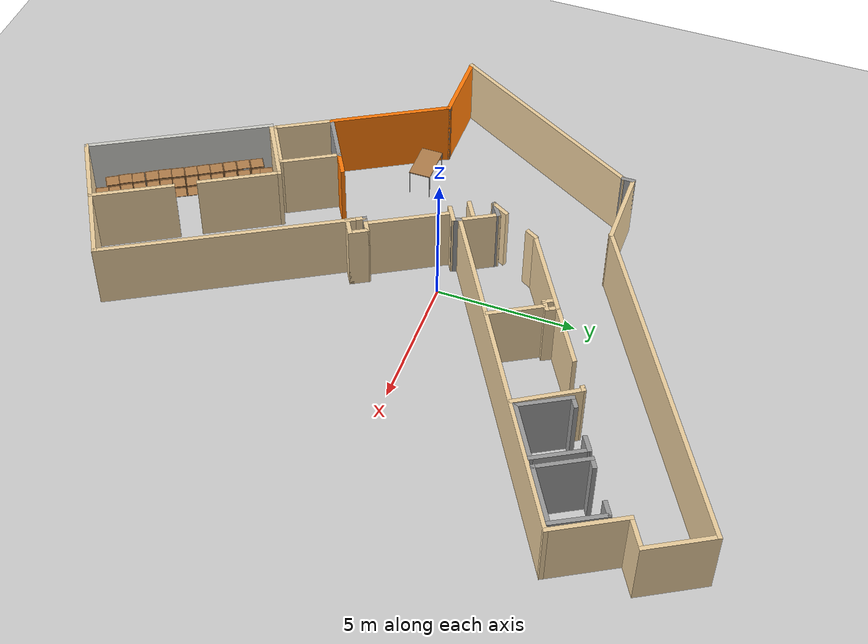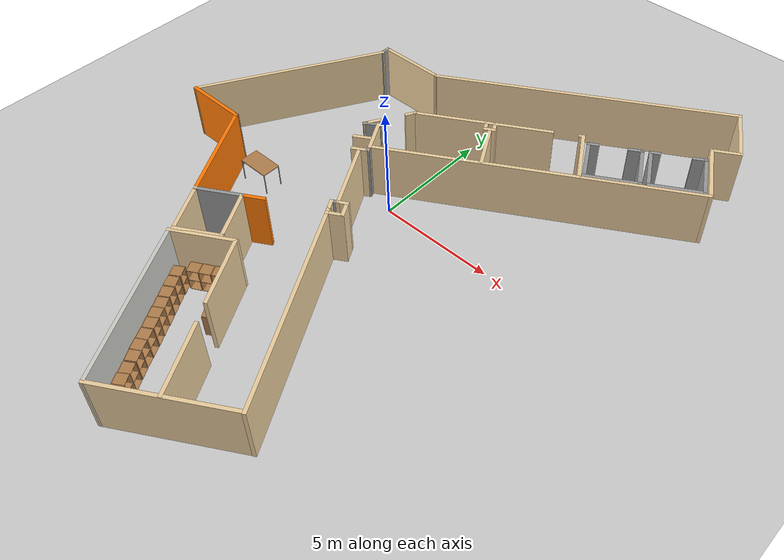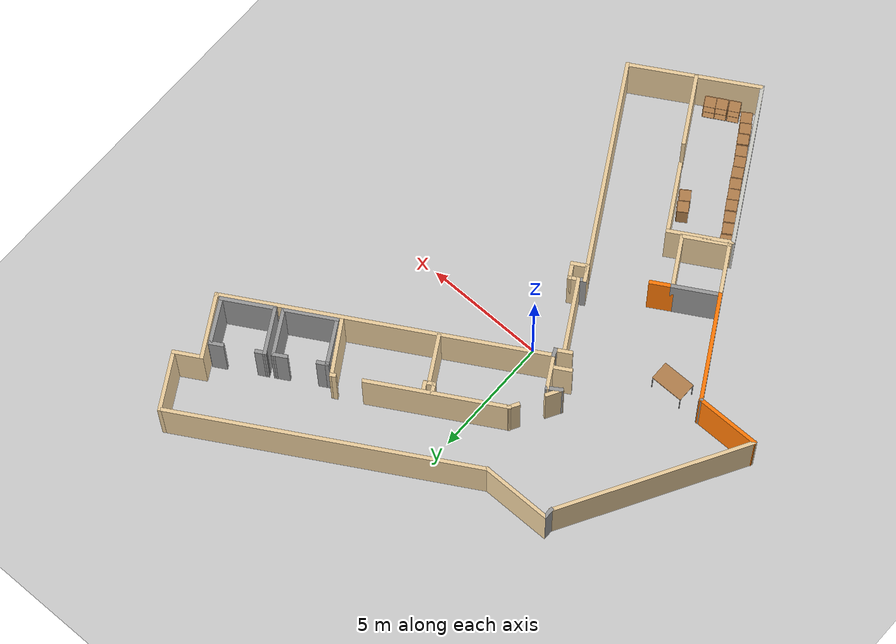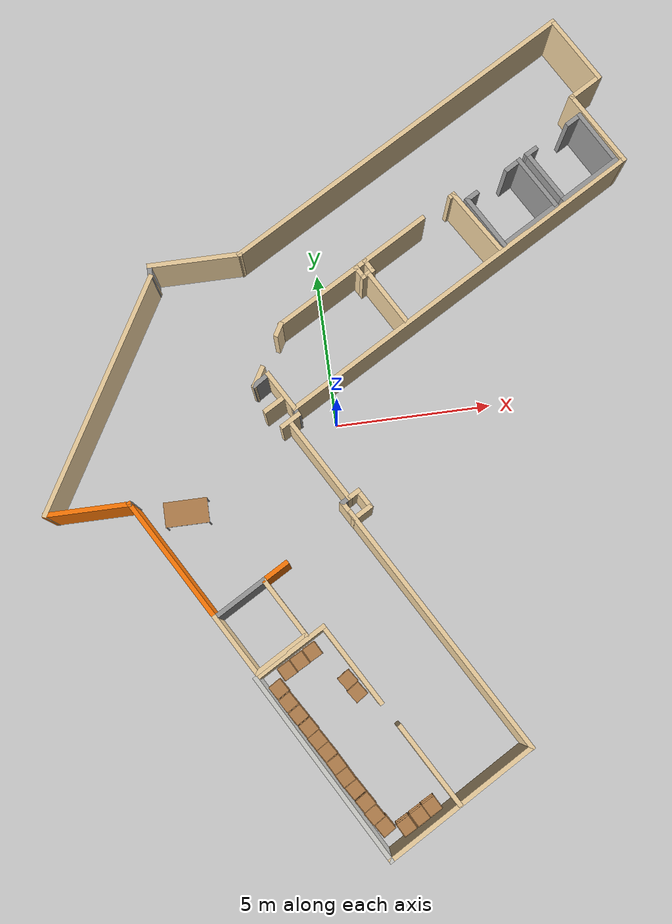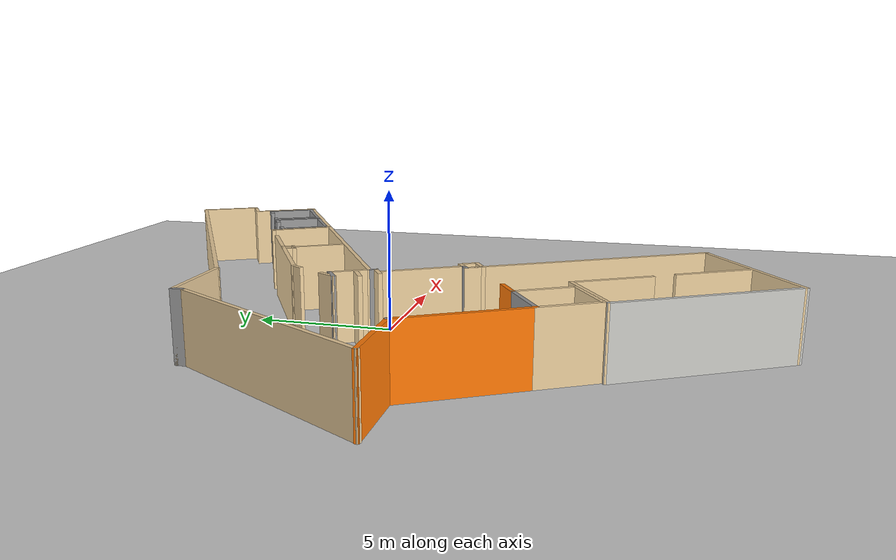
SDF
<sdf version="1.6">
 <world name="default">
  <light name="sun" type="directional">
   <pose>0 0 10 0 -0 0</pose>
   <diffuse>0.8 0.8 0.8 1</diffuse>
   <specular>0.1 0.1 0.1 1</specular>
   <attenuation>
    <range>1000</range>
    <constant>0.9</constant>
    <linear>0.01</linear>
    <quadratic>0.001</quadratic>
   </attenuation>
   <direction>-0.5 0.5 -1</direction>
  </light>
  <model name="ground_plane">
   <static>1</static>
   <link name="link">
    <collision name="collision">
     <geometry><plane><normal>0 0 1</normal><size>100 100</size></plane></geometry>
     <surface><friction><ode><mu>100</mu><mu2>50</mu2></ode></friction></surface>
    </collision>
    <visual name="visual">
     <cast_shadows>0</cast_shadows>
     <geometry><plane><normal>0 0 1</normal><size>100 100</size></plane></geometry>
     <material>
      <script><uri>file://media/materials/scripts/gazebo.material</uri><name>Gazebo/Grey</name></script>
     </material>
    </visual>
   </link>
  </model>
  <gravity>0 0 -9.8</gravity>
  <magnetic_field>6e-06 2.3e-05 -4.2e-05</magnetic_field>
  <atmosphere type="adiabatic"/>
  <physics name="default_physics" default="0" type="ode">
   <max_step_size>0.001</max_step_size>
   <real_time_factor>1</real_time_factor>
   <real_time_update_rate>1000</real_time_update_rate>
  </physics>
  <scene><ambient>0.4 0.4 0.4 1</ambient><background>0.7 0.7 0.7 1</background><shadows>1</shadows></scene>
  <spherical_coordinates>
   <surface_model>EARTH_WGS84</surface_model>
   <latitude_deg>0</latitude_deg>
   <longitude_deg>0</longitude_deg>
   <elevation>0</elevation>
   <heading_deg>0</heading_deg>
  </spherical_coordinates>
  <model name="my_office_no_item">
   <pose>0.40615 -0.88123 0 0 -0 0</pose>
   <link name="Wall_10">
    <collision name="Wall_10_Collision">
     <geometry><box><size>6.81721 0.15 2.5</size></box></geometry>
     <pose>0 0 1.25 0 -0 0</pose>
    </collision>
    <visual name="Wall_10_Visual">
     <pose>0 0 1.25 0 -0 0</pose>
     <geometry><box><size>6.81721 0.15 2.5</size></box></geometry>
     <material>
      <script><uri>file://media/materials/scripts/gazebo.material</uri><name>Gazebo/CeilingTiled</name></script>
      <ambient>0.921569 0.807843 0.615686 1</ambient>
     </material>
    </visual>
    <pose>-2.24104 -9.70627 0 0 0 -1.05271</pose>
   </link>
   <link name="Wall_100">
    <collision name="Wall_100_Collision">
     <geometry><box><size>1.5 0.15 2.5</size></box></geometry>
     <pose>0 0 1.25 0 -0 0</pose>
    </collision>
    <visual name="Wall_100_Visual">
     <pose>0 0 1.25 0 -0 0</pose>
     <geometry><box><size>1.5 0.15 2.5</size></box></geometry>
     <material>
      <script><uri>file://media/materials/scripts/gazebo.material</uri><name>Gazebo/Grey</name></script>
      <ambient>0.921569 0.807843 0.615686 1</ambient>
     </material>
    </visual>
    <pose>-2.01529 1.80028 0 0 -0 2.0944</pose>
   </link>
   <link name="Wall_101">
    <collision name="Wall_101_Collision">
     <geometry><box><size>0.704824 0.15 2.5</size></box></geometry>
     <pose>0 0 1.25 0 -0 0</pose>
    </collision>
    <visual name="Wall_101_Visual">
     <pose>0 0 1.25 0 -0 0</pose>
     <geometry><box><size>0.704824 0.15 2.5</size></box></geometry>
     <material>
      <script><uri>file://media/materials/scripts/gazebo.material</uri><name>Gazebo/Grey</name></script>
      <ambient>1 1 1 1</ambient>
     </material>
    </visual>
    <pose>-2.58645 2.23531 0 0 0 -2.5723</pose>
   </link>
   <link name="Wall_103">
    <collision name="Wall_103_Collision">
     <geometry><box><size>0.75 0.15 2.5</size></box></geometry>
     <pose>0 0 1.25 0 -0 0</pose>
    </collision>
    <visual name="Wall_103_Visual">
     <pose>0 0 1.25 0 -0 0</pose>
     <geometry><box><size>0.75 0.15 2.5</size></box></geometry>
     <material>
      <script><uri>file://media/materials/scripts/gazebo.material</uri><name>Gazebo/Grey</name></script>
      <ambient>0.921569 0.807843 0.615686 1</ambient>
     </material>
    </visual>
    <pose>-2.30972 1.40421 0 0 -0 0.523599</pose>
   </link>
   <link name="Wall_105">
    <collision name="Wall_105_Collision">
     <geometry><box><size>0.75 0.15 2.5</size></box></geometry>
     <pose>0 0 1.25 0 -0 0</pose>
    </collision>
    <visual name="Wall_105_Visual">
     <pose>0 0 1.25 0 -0 0</pose>
     <geometry><box><size>0.75 0.15 2.5</size></box></geometry>
     <material>
      <script><uri>file://media/materials/scripts/gazebo.material</uri><name>Gazebo/Grey</name></script>
      <ambient>0.921569 0.807843 0.615686 1</ambient>
     </material>
    </visual>
    <pose>-1.85346 0.856693 0 0 -0 0.523599</pose>
   </link>
   <link name="Wall_107">
    <collision name="Wall_107_Collision">
     <geometry><box><size>0.375318 0.15 2.5</size></box></geometry>
     <pose>0 0 1.25 0 -0 0</pose>
    </collision>
    <visual name="Wall_107_Visual">
     <pose>0 0 1.25 0 -0 0</pose>
     <geometry><box><size>0.375318 0.15 2.5</size></box></geometry>
     <material>
      <script><uri>file://media/materials/scripts/gazebo.material</uri><name>Gazebo/Grey</name></script>
      <ambient>1 1 1 1</ambient>
     </material>
    </visual>
    <pose>-1.63572 1.1112 0 0 -0 1.9535</pose>
   </link>
   <link name="Wall_114">
    <collision name="Wall_114_Collision">
     <geometry><box><size>3 0.15 2.5</size></box></geometry>
     <pose>0 0 1.25 0 -0 0</pose>
    </collision>
    <visual name="Wall_114_Visual">
     <pose>0 0 1.25 0 -0 0</pose>
     <geometry><box><size>3 0.15 2.5</size></box></geometry>
     <material>
      <script><uri>file://media/materials/scripts/gazebo.material</uri><name>Gazebo/Grey</name></script>
      <ambient>0.921569 0.807843 0.615686 1</ambient>
     </material>
    </visual>
    <pose>-1.09613 -0.526424 0 0 -0 2.0944</pose>
   </link>
   <link name="Wall_118">
    <collision name="Wall_118_Collision">
     <geometry><box><size>0.5 0.15 2.5</size></box></geometry>
     <pose>0 0 1.25 0 -0 0</pose>
    </collision>
    <visual name="Wall_118_Visual">
     <pose>0 0 1.25 0 -0 0</pose>
     <geometry><box><size>0.5 0.15 2.5</size></box></geometry>
     <material>
      <script><uri>file://media/materials/scripts/gazebo.material</uri><name>Gazebo/Grey</name></script>
      <ambient>0.921569 0.807843 0.615686 1</ambient>
     </material>
    </visual>
    <pose>-0.232079 -1.67301 0 0 -0 0.523599</pose>
   </link>
   <link name="Wall_119">
    <collision name="Wall_119_Collision">
     <geometry><box><size>0.75 0.15 2.5</size></box></geometry>
     <pose>0 0 1.25 0 -0 0</pose>
    </collision>
    <visual name="Wall_119_Visual">
     <pose>0 0 1.25 0 -0 0</pose>
     <geometry><box><size>0.75 0.15 2.5</size></box></geometry>
     <material>
      <script><uri>file://media/materials/scripts/gazebo.material</uri><name>Gazebo/Grey</name></script>
      <ambient>0.921569 0.807843 0.615686 1</ambient>
     </material>
    </visual>
    <pose>0.069475 -1.84532 0 0 0 -1.0472</pose>
   </link>
   <link name="Wall_12">
    <collision name="Wall_12_Collision">
     <geometry><box><size>2.7 0.15 2.5</size></box></geometry>
     <pose>0 0 1.25 0 -0 0</pose>
    </collision>
    <visual name="Wall_12_Visual">
     <pose>0 0 1.25 0 -0 0</pose>
     <geometry><box><size>2.7 0.15 2.5</size></box></geometry>
     <material>
      <script><uri>file://media/materials/scripts/gazebo.material</uri><name>Gazebo/Grey</name></script>
      <ambient>0.921569 0.807843 0.615686 1</ambient>
     </material>
    </visual>
    <pose>-2.78771 -6.17263 0 0 -0 0.523599</pose>
   </link>
   <link name="Wall_121">
    <collision name="Wall_121_Collision">
     <geometry><box><size>0.75 0.15 2.5</size></box></geometry>
     <pose>0 0 1.25 0 -0 0</pose>
    </collision>
    <visual name="Wall_121_Visual">
     <pose>0 0 1.25 0 -0 0</pose>
     <geometry><box><size>0.75 0.15 2.5</size></box></geometry>
     <material>
      <script><uri>file://media/materials/scripts/gazebo.material</uri><name>Gazebo/Grey</name></script>
      <ambient>0.921569 0.807843 0.615686 1</ambient>
     </material>
    </visual>
    <pose>-0.040333 -2.25513 0 0 0 -2.61799</pose>
   </link>
   <link name="Wall_127">
    <collision name="Wall_127_Collision">
     <geometry><box><size>0.75 0.15 2.5</size></box></geometry>
     <pose>0 0 1.25 0 -0 0</pose>
    </collision>
    <visual name="Wall_127_Visual">
     <pose>0 0 1.25 0 -0 0</pose>
     <geometry><box><size>0.75 0.15 2.5</size></box></geometry>
     <material>
      <script><uri>file://media/materials/scripts/gazebo.material</uri><name>Gazebo/Grey</name></script>
      <ambient>0.921569 0.807843 0.615686 1</ambient>
     </material>
    </visual>
    <pose>-0.45014 -2.14532 0 0 -0 2.0944</pose>
   </link>
   <link name="Wall_128">
    <collision name="Wall_128_Collision">
     <geometry><box><size>0.4 0.15 2.5</size></box></geometry>
     <pose>0 0 1.25 0 -0 0</pose>
    </collision>
    <visual name="Wall_128_Visual">
     <pose>0 0 1.25 0 -0 0</pose>
     <geometry><box><size>0.4 0.15 2.5</size></box></geometry>
     <material>
      <script><uri>file://media/materials/scripts/gazebo.material</uri><name>Gazebo/Grey</name></script>
      <ambient>1 1 1 1</ambient>
     </material>
    </visual>
    <pose>-0.491887 -1.82301 0 0 -0 0.523599</pose>
   </link>
   <link name="Wall_130">
    <collision name="Wall_130_Collision">
     <geometry><box><size>2 0.15 2.5</size></box></geometry>
     <pose>0 0 1.25 0 -0 0</pose>
    </collision>
    <visual name="Wall_130_Visual">
     <pose>0 0 1.25 0 -0 0</pose>
     <geometry><box><size>2 0.15 2.5</size></box></geometry>
     <material>
      <script><uri>file://media/materials/scripts/gazebo.material</uri><name>Gazebo/Grey</name></script>
      <ambient>0.921569 0.807843 0.615686 1</ambient>
     </material>
    </visual>
    <pose>1.6661 4.2808 0 0 -0 2.0944</pose>
   </link>
   <link name="Wall_132">
    <collision name="Wall_132_Collision">
     <geometry><box><size>0.5 0.15 2.5</size></box></geometry>
     <pose>0 0 1.25 0 -0 0</pose>
    </collision>
    <visual name="Wall_132_Visual">
     <pose>0 0 1.25 0 -0 0</pose>
     <geometry><box><size>0.5 0.15 2.5</size></box></geometry>
     <material>
      <script><uri>file://media/materials/scripts/gazebo.material</uri><name>Gazebo/Grey</name></script>
      <ambient>0.921569 0.807843 0.615686 1</ambient>
     </material>
    </visual>
    <pose>0.900947 5.21621 0 0 0 -1.0472</pose>
   </link>
   <link name="Wall_133">
    <collision name="Wall_133_Collision">
     <geometry><box><size>0.5 0.15 2.5</size></box></geometry>
     <pose>0 0 1.25 0 -0 0</pose>
    </collision>
    <visual name="Wall_133_Visual">
     <pose>0 0 1.25 0 -0 0</pose>
     <geometry><box><size>0.5 0.15 2.5</size></box></geometry>
     <material>
      <script><uri>file://media/materials/scripts/gazebo.material</uri><name>Gazebo/Grey</name></script>
      <ambient>0.921569 0.807843 0.615686 1</ambient>
     </material>
    </visual>
    <pose>1.14 5.15215 0 0 -0 0.523599</pose>
   </link>
   <link name="Wall_134">
    <collision name="Wall_134_Collision">
     <geometry><box><size>0.5 0.15 2.5</size></box></geometry>
     <pose>0 0 1.25 0 -0 0</pose>
    </collision>
    <visual name="Wall_134_Visual">
     <pose>0 0 1.25 0 -0 0</pose>
     <geometry><box><size>0.5 0.15 2.5</size></box></geometry>
     <material>
      <script><uri>file://media/materials/scripts/gazebo.material</uri><name>Gazebo/Grey</name></script>
      <ambient>0.921569 0.807843 0.615686 1</ambient>
     </material>
    </visual>
    <pose>1.20406 5.39121 0 0 -0 2.0944</pose>
   </link>
   <link name="Wall_138">
    <collision name="Wall_138_Collision">
     <geometry><box><size>0.5 0.15 2.5</size></box></geometry>
     <pose>0 0 1.25 0 -0 0</pose>
    </collision>
    <visual name="Wall_138_Visual">
     <pose>0 0 1.25 0 -0 0</pose>
     <geometry><box><size>0.5 0.15 2.5</size></box></geometry>
     <material>
      <script><uri>file://media/materials/scripts/gazebo.material</uri><name>Gazebo/Grey</name></script>
      <ambient>0.921569 0.807843 0.615686 1</ambient>
     </material>
    </visual>
    <pose>-1.85761 3.75287 0 0 0 -2.0944</pose>
   </link>
   <link name="Wall_140">
    <collision name="Wall_140_Collision">
     <geometry><box><size>0.75 0.15 2.5</size></box></geometry>
     <pose>0 0 1.25 0 -0 0</pose>
    </collision>
    <visual name="Wall_140_Visual">
     <pose>0 0 1.25 0 -0 0</pose>
     <geometry><box><size>0.75 0.15 2.5</size></box></geometry>
     <material>
      <script><uri>file://media/materials/scripts/gazebo.material</uri><name>Gazebo/Grey</name></script>
      <ambient>0.921569 0.807843 0.615686 1</ambient>
     </material>
    </visual>
    <pose>-2.67011 2.34558 0 0 -0 1.0472</pose>
   </link>
   <link name="Wall_142">
    <collision name="Wall_142_Collision">
     <geometry><box><size>5.75 0.15 2.5</size></box></geometry>
     <pose>0 0 1.25 0 -0 0</pose>
    </collision>
    <visual name="Wall_142_Visual">
     <pose>0 0 1.25 0 -0 0</pose>
     <geometry><box><size>5.75 0.15 2.5</size></box></geometry>
     <material>
      <script><uri>file://media/materials/scripts/gazebo.material</uri><name>Gazebo/Grey</name></script>
      <ambient>0.921569 0.807843 0.615686 1</ambient>
     </material>
    </visual>
    <pose>0.654765 5.30443 0 0 -0 0.523599</pose>
   </link>
   <link name="Wall_144">
    <collision name="Wall_144_Collision">
     <geometry><box><size>0.25 0.15 2.5</size></box></geometry>
     <pose>0 0 1.25 0 -0 0</pose>
    </collision>
    <visual name="Wall_144_Visual">
     <pose>0 0 1.25 0 -0 0</pose>
     <geometry><box><size>0.25 0.15 2.5</size></box></geometry>
     <material>
      <script><uri>file://media/materials/scripts/gazebo.material</uri><name>Gazebo/Grey</name></script>
      <ambient>0.921569 0.807843 0.615686 1</ambient>
     </material>
    </visual>
    <pose>4.11887 7.30443 0 0 0 -2.61799</pose>
   </link>
   <link name="Wall_146">
    <collision name="Wall_146_Collision">
     <geometry><box><size>1 0.15 2.5</size></box></geometry>
     <pose>0 0 1.25 0 -0 0</pose>
    </collision>
    <visual name="Wall_146_Visual">
     <pose>0 0 1.25 0 -0 0</pose>
     <geometry><box><size>1 0.15 2.5</size></box></geometry>
     <material>
      <script><uri>file://media/materials/scripts/gazebo.material</uri><name>Gazebo/Grey</name></script>
      <ambient>0.996078 0.47451 0.0196078 1</ambient>
     </material>
    </visual>
    <pose>-2.92194 -3.69198 0 0 -0 0.523599</pose>
   </link>
   <link name="Wall_148">
    <collision name="Wall_148_Collision">
     <geometry><box><size>3 0.15 2.5</size></box></geometry>
     <pose>0 0 1.25 0 -0 0</pose>
    </collision>
    <visual name="Wall_148_Visual">
     <pose>0 0 1.25 0 -0 0</pose>
     <geometry><box><size>3 0.15 2.5</size></box></geometry>
     <material>
      <script><uri>file://media/materials/scripts/gazebo.material</uri><name>Gazebo/Grey</name></script>
      <ambient>0.921569 0.807843 0.615686 1</ambient>
     </material>
    </visual>
    <pose>-0.971033 -6.76922 0 0 0 -1.0472</pose>
   </link>
   <link name="Wall_151">
    <collision name="Wall_151_Collision">
     <geometry><box><size>3 0.15 2.5</size></box></geometry>
     <pose>0 0 1.25 0 -0 0</pose>
    </collision>
    <visual name="Wall_151_Visual">
     <pose>0 0 1.25 0 -0 0</pose>
     <geometry><box><size>3 0.15 2.5</size></box></geometry>
     <material>
      <script><uri>file://media/materials/scripts/gazebo.material</uri><name>Gazebo/Grey</name></script>
      <ambient>0.921569 0.807843 0.615686 1</ambient>
     </material>
    </visual>
    <pose>0.936909 -10.0288 0 0 0 -1.0472</pose>
   </link>
   <link name="Wall_20">
    <collision name="Wall_20_Collision">
     <geometry><box><size>2 0.15 2.5</size></box></geometry>
     <pose>0 0 1.25 0 -0 0</pose>
    </collision>
    <visual name="Wall_20_Visual">
     <pose>0 0 1.25 0 -0 0</pose>
     <geometry><box><size>2 0.15 2.5</size></box></geometry>
     <material>
      <script><uri>file://media/materials/scripts/gazebo.material</uri><name>Gazebo/Grey</name></script>
      <ambient>0.921569 0.807843 0.615686 1</ambient>
     </material>
    </visual>
    <pose>-3.04107 -6.18563 0 0 -0 0.523599</pose>
   </link>
   <link name="Wall_23">
    <collision name="Wall_23_Collision">
     <geometry><box><size>2.25 0.15 2.5</size></box></geometry>
     <pose>0 0 1.25 0 -0 0</pose>
    </collision>
    <visual name="Wall_23_Visual">
     <pose>0 0 1.25 0 -0 0</pose>
     <geometry><box><size>2.25 0.15 2.5</size></box></geometry>
     <material>
      <script><uri>file://media/materials/scripts/gazebo.material</uri><name>Gazebo/Grey</name></script>
      <ambient>0.921569 0.807843 0.615686 1</ambient>
     </material>
    </visual>
    <pose>-4.36715 -5.73881 0 0 -0 2.0944</pose>
   </link>
   <link name="Wall_24">
    <collision name="Wall_24_Collision">
     <geometry><box><size>2 0.15 2.5</size></box></geometry>
     <pose>0 0 1.25 0 -0 0</pose>
    </collision>
    <visual name="Wall_24_Visual">
     <pose>0 0 1.25 0 -0 0</pose>
     <geometry><box><size>2 0.15 2.5</size></box></geometry>
     <material>
      <script><uri>file://media/materials/scripts/gazebo.material</uri><name>Gazebo/Grey</name></script>
      <ambient>1 1 1 1</ambient>
     </material>
    </visual>
    <pose>-4.09107 -4.36698 0 0 -0 0.523599</pose>
   </link>
   <link name="Wall_25">
    <collision name="Wall_25_Collision">
     <geometry><box><size>2.25 0.15 2.5</size></box></geometry>
     <pose>0 0 1.25 0 -0 0</pose>
    </collision>
    <visual name="Wall_25_Visual">
     <pose>0 0 1.25 0 -0 0</pose>
     <geometry><box><size>2.25 0.15 2.5</size></box></geometry>
     <material>
      <script><uri>file://media/materials/scripts/gazebo.material</uri><name>Gazebo/Grey</name></script>
      <ambient>0.921569 0.807843 0.615686 1</ambient>
     </material>
    </visual>
    <pose>-2.765 -4.81381 0 0 0 -1.0472</pose>
   </link>
   <link name="Wall_28">
    <collision name="Wall_28_Collision">
     <geometry><box><size>9.03253 0.15 2.5</size></box></geometry>
     <pose>0 0 1.25 0 -0 0</pose>
    </collision>
    <visual name="Wall_28_Visual">
     <pose>0 0 1.25 0 -0 0</pose>
     <geometry><box><size>9.03253 0.15 2.5</size></box></geometry>
     <material>
      <script><uri>file://media/materials/scripts/gazebo.material</uri><name>Gazebo/Grey</name></script>
      <ambient>0.921569 0.807843 0.615686 1</ambient>
     </material>
    </visual>
    <pose>1.81712 -6.06844 0 0 0 -1.04842</pose>
   </link>
   <link name="Wall_30">
    <collision name="Wall_30_Collision">
     <geometry><box><size>4.5 0.15 2.5</size></box></geometry>
     <pose>0 0 1.25 0 -0 0</pose>
    </collision>
    <visual name="Wall_30_Visual">
     <pose>0 0 1.25 0 -0 0</pose>
     <geometry><box><size>4.5 0.15 2.5</size></box></geometry>
     <material>
      <script><uri>file://media/materials/scripts/gazebo.material</uri><name>Gazebo/Grey</name></script>
      <ambient>0.996078 0.47451 0.0196078 1</ambient>
     </material>
    </visual>
    <pose>-5.97965 -2.94587 0 0 -0 2.0944</pose>
   </link>
   <link name="Wall_31">
    <collision name="Wall_31_Collision">
     <geometry><box><size>0.15 0.15 2.5</size></box></geometry>
     <pose>0 0 1.25 0 -0 0</pose>
    </collision>
    <visual name="Wall_31_Visual">
     <pose>0 0 1.25 0 -0 0</pose>
     <geometry><box><size>0.15 0.15 2.5</size></box></geometry>
     <material>
      <script><uri>file://media/materials/scripts/gazebo.material</uri><name>Gazebo/Grey</name></script>
      <ambient>1 1 1 1</ambient>
     </material>
    </visual>
    <pose>-7.06715 -1.06227 0 0 -0 0</pose>
   </link>
   <link name="Wall_34">
    <collision name="Wall_34_Collision">
     <geometry><box><size>2.75 0.15 2.5</size></box></geometry>
     <pose>0 0 1.25 0 -0 0</pose>
    </collision>
    <visual name="Wall_34_Visual">
     <pose>0 0 1.25 0 -0 0</pose>
     <geometry><box><size>2.75 0.15 2.5</size></box></geometry>
     <material>
      <script><uri>file://media/materials/scripts/gazebo.material</uri><name>Gazebo/Grey</name></script>
      <ambient>0.996078 0.47451 0.0196078 1</ambient>
     </material>
    </visual>
    <pose>-8.36715 -1.06227 0 0 -0 3.14159</pose>
   </link>
   <link name="Wall_35">
    <collision name="Wall_35_Collision">
     <geometry><box><size>8.25 0.15 2.5</size></box></geometry>
     <pose>0 0 1.25 0 -0 0</pose>
    </collision>
    <visual name="Wall_35_Visual">
     <pose>0 0 1.25 0 -0 0</pose>
     <geometry><box><size>8.25 0.15 2.5</size></box></geometry>
     <material>
      <script><uri>file://media/materials/scripts/gazebo.material</uri><name>Gazebo/Grey</name></script>
      <ambient>0.921569 0.807843 0.615686 1</ambient>
     </material>
    </visual>
    <pose>-7.64215 2.44513 0 0 -0 1.0472</pose>
   </link>
   <link name="Wall_37">
    <collision name="Wall_37_Collision">
     <geometry><box><size>0.5 0.15 2.5</size></box></geometry>
     <pose>0 0 1.25 0 -0 0</pose>
    </collision>
    <visual name="Wall_37_Visual">
     <pose>0 0 1.25 0 -0 0</pose>
     <geometry><box><size>0.5 0.15 2.5</size></box></geometry>
     <material>
      <script><uri>file://media/materials/scripts/gazebo.material</uri><name>Gazebo/Grey</name></script>
      <ambient>1 1 1 1</ambient>
     </material>
    </visual>
    <pose>-5.61715 6.12754 0 0 -0 1.5708</pose>
   </link>
   <link name="Wall_38">
    <collision name="Wall_38_Collision">
     <geometry><box><size>3 0.15 2.5</size></box></geometry>
     <pose>0 0 1.25 0 -0 0</pose>
    </collision>
    <visual name="Wall_38_Visual">
     <pose>0 0 1.25 0 -0 0</pose>
     <geometry><box><size>3 0.15 2.5</size></box></geometry>
     <material>
      <script><uri>file://media/materials/scripts/gazebo.material</uri><name>Gazebo/Grey</name></script>
      <ambient>0.921569 0.807843 0.615686 1</ambient>
     </material>
    </visual>
    <pose>-4.19215 6.30254 0 0 -0 0</pose>
   </link>
   <link name="Wall_39">
    <collision name="Wall_39_Collision">
     <geometry><box><size>12.75 0.15 2.5</size></box></geometry>
     <pose>0 0 1.25 0 -0 0</pose>
    </collision>
    <visual name="Wall_39_Visual">
     <pose>0 0 1.25 0 -0 0</pose>
     <geometry><box><size>12.75 0.15 2.5</size></box></geometry>
     <material>
      <script><uri>file://media/materials/scripts/gazebo.material</uri><name>Gazebo/Grey</name></script>
      <ambient>0.921569 0.807843 0.615686 1</ambient>
     </material>
    </visual>
    <pose>2.68881 9.45254 0 0 -0 0.523599</pose>
   </link>
   <link name="Wall_41">
    <collision name="Wall_41_Collision">
     <geometry><box><size>2.5 0.15 2.5</size></box></geometry>
     <pose>0 0 1.25 0 -0 0</pose>
    </collision>
    <visual name="Wall_41_Visual">
     <pose>0 0 1.25 0 -0 0</pose>
     <geometry><box><size>2.5 0.15 2.5</size></box></geometry>
     <material>
      <script><uri>file://media/materials/scripts/gazebo.material</uri><name>Gazebo/Grey</name></script>
      <ambient>0.921569 0.807843 0.615686 1</ambient>
     </material>
    </visual>
    <pose>8.73227 11.585 0 0 0 -1.0472</pose>
   </link>
   <link name="Wall_42">
    <collision name="Wall_42_Collision">
     <geometry><box><size>1.25 0.15 2.5</size></box></geometry>
     <pose>0 0 1.25 0 -0 0</pose>
    </collision>
    <visual name="Wall_42_Visual">
     <pose>0 0 1.25 0 -0 0</pose>
     <geometry><box><size>1.25 0.15 2.5</size></box></geometry>
     <material>
      <script><uri>file://media/materials/scripts/gazebo.material</uri><name>Gazebo/Grey</name></script>
      <ambient>0.921569 0.807843 0.615686 1</ambient>
     </material>
    </visual>
    <pose>8.84346 10.2924 0 0 0 -2.61799</pose>
   </link>
   <link name="Wall_46">
    <collision name="Wall_46_Collision">
     <geometry><box><size>1.98692 0.15 2.5</size></box></geometry>
     <pose>0 0 1.25 0 -0 0</pose>
    </collision>
    <visual name="Wall_46_Visual">
     <pose>0 0 1.25 0 -0 0</pose>
     <geometry><box><size>1.98692 0.15 2.5</size></box></geometry>
     <material>
      <script><uri>file://media/materials/scripts/gazebo.material</uri><name>Gazebo/Grey</name></script>
      <ambient>1 1 1 1</ambient>
     </material>
    </visual>
    <pose>8.96637 8.57534 0 0 0 -1.05967</pose>
   </link>
   <link name="Wall_47">
    <collision name="Wall_47_Collision">
     <geometry><box><size>2.25 0.15 2.5</size></box></geometry>
     <pose>0 0 1.25 0 -0 0</pose>
    </collision>
    <visual name="Wall_47_Visual">
     <pose>0 0 1.25 0 -0 0</pose>
     <geometry><box><size>2.25 0.15 2.5</size></box></geometry>
     <material>
      <script><uri>file://media/materials/scripts/gazebo.material</uri><name>Gazebo/Grey</name></script>
      <ambient>1 1 1 1</ambient>
     </material>
    </visual>
    <pose>8.50632 7.24926 0 0 0 -2.61799</pose>
   </link>
   <link name="Wall_48">
    <collision name="Wall_48_Collision">
     <geometry><box><size>2 0.15 2.5</size></box></geometry>
     <pose>0 0 1.25 0 -0 0</pose>
    </collision>
    <visual name="Wall_48_Visual">
     <pose>0 0 1.25 0 -0 0</pose>
     <geometry><box><size>2 0.15 2.5</size></box></geometry>
     <material>
      <script><uri>file://media/materials/scripts/gazebo.material</uri><name>Gazebo/Grey</name></script>
      <ambient>1 1 1 1</ambient>
     </material>
    </visual>
    <pose>7.13449 7.52534 0 0 -0 2.0944</pose>
   </link>
   <link name="Wall_50">
    <collision name="Wall_50_Collision">
     <geometry><box><size>0.462497 0.15 2.5</size></box></geometry>
     <pose>0 0 1.25 0 -0 0</pose>
    </collision>
    <visual name="Wall_50_Visual">
     <pose>0 0 1.25 0 -0 0</pose>
     <geometry><box><size>0.462497 0.15 2.5</size></box></geometry>
     <material>
      <script><uri>file://media/materials/scripts/gazebo.material</uri><name>Gazebo/Grey</name></script>
      <ambient>1 1 1 1</ambient>
     </material>
    </visual>
    <pose>6.80843 8.40257 0 0 -0 0.509127</pose>
   </link>
   <link name="Wall_52">
    <collision name="Wall_52_Collision">
     <geometry><box><size>0.6 0.15 2.5</size></box></geometry>
     <pose>0 0 1.25 0 -0 0</pose>
    </collision>
    <visual name="Wall_52_Visual">
     <pose>0 0 1.25 0 -0 0</pose>
     <geometry><box><size>0.6 0.15 2.5</size></box></geometry>
     <material>
      <script><uri>file://media/materials/scripts/gazebo.material</uri><name>Gazebo/Grey</name></script>
      <ambient>1 1 1 1</ambient>
     </material>
    </visual>
    <pose>8.30902 9.26391 0 0 0 -2.61799</pose>
   </link>
   <link name="Wall_63">
    <collision name="Wall_63_Collision">
     <geometry><box><size>2 0.15 2.5</size></box></geometry>
     <pose>0 0 1.25 0 -0 0</pose>
    </collision>
    <visual name="Wall_63_Visual">
     <pose>0 0 1.25 0 -0 0</pose>
     <geometry><box><size>2 0.15 2.5</size></box></geometry>
     <material>
      <script><uri>file://media/materials/scripts/gazebo.material</uri><name>Gazebo/Grey</name></script>
      <ambient>1 1 1 1</ambient>
     </material>
    </visual>
    <pose>6.84954 7.3586 0 0 0 -1.0472</pose>
   </link>
   <link name="Wall_64">
    <collision name="Wall_64_Collision">
     <geometry><box><size>2.25 0.15 2.5</size></box></geometry>
     <pose>0 0 1.25 0 -0 0</pose>
    </collision>
    <visual name="Wall_64_Visual">
     <pose>0 0 1.25 0 -0 0</pose>
     <geometry><box><size>2.25 0.15 2.5</size></box></geometry>
     <material>
      <script><uri>file://media/materials/scripts/gazebo.material</uri><name>Gazebo/Grey</name></script>
      <ambient>1 1 1 1</ambient>
     </material>
    </visual>
    <pose>6.40272 6.03253 0 0 0 -2.61799</pose>
   </link>
   <link name="Wall_65">
    <collision name="Wall_65_Collision">
     <geometry><box><size>2 0.15 2.5</size></box></geometry>
     <pose>0 0 1.25 0 -0 0</pose>
    </collision>
    <visual name="Wall_65_Visual">
     <pose>0 0 1.25 0 -0 0</pose>
     <geometry><box><size>2 0.15 2.5</size></box></geometry>
     <material>
      <script><uri>file://media/materials/scripts/gazebo.material</uri><name>Gazebo/Grey</name></script>
      <ambient>1 1 1 1</ambient>
     </material>
    </visual>
    <pose>5.04089 6.3086 0 0 -0 2.0944</pose>
   </link>
   <link name="Wall_68">
    <collision name="Wall_68_Collision">
     <geometry><box><size>0.5 0.15 2.5</size></box></geometry>
     <pose>0 0 1.25 0 -0 0</pose>
    </collision>
    <visual name="Wall_68_Visual">
     <pose>0 0 1.25 0 -0 0</pose>
     <geometry><box><size>0.5 0.15 2.5</size></box></geometry>
     <material>
      <script><uri>file://media/materials/scripts/gazebo.material</uri><name>Gazebo/Grey</name></script>
      <ambient>1 1 1 1</ambient>
     </material>
    </visual>
    <pose>4.72994 7.19717 0 0 -0 0.523599</pose>
   </link>
   <link name="Wall_7">
    <collision name="Wall_7_Collision">
     <geometry><box><size>5.49275 0.15 2.5</size></box></geometry>
     <pose>0 0 1.25 0 -0 0</pose>
    </collision>
    <visual name="Wall_7_Visual">
     <pose>0 0 1.25 0 -0 0</pose>
     <geometry><box><size>5.49275 0.15 2.5</size></box></geometry>
     <material>
      <script><uri>file://media/materials/scripts/gazebo.material</uri><name>Gazebo/Grey</name></script>
      <ambient>0.921569 0.807843 0.615686 1</ambient>
     </material>
    </visual>
    <pose>1.71643 -11.2549 0 0 -0 0.528712</pose>
   </link>
   <link name="Wall_72">
    <collision name="Wall_72_Collision">
     <geometry><box><size>0.637557 0.15 2.5</size></box></geometry>
     <pose>0 0 1.25 0 -0 0</pose>
    </collision>
    <visual name="Wall_72_Visual">
     <pose>0 0 1.25 0 -0 0</pose>
     <geometry><box><size>0.637557 0.15 2.5</size></box></geometry>
     <material>
      <script><uri>file://media/materials/scripts/gazebo.material</uri><name>Gazebo/Grey</name></script>
      <ambient>1 1 1 1</ambient>
     </material>
    </visual>
    <pose>6.17707 8.03583 0 0 0 -2.60872</pose>
   </link>
   <link name="Wall_78">
    <collision name="Wall_78_Collision">
     <geometry><box><size>2.75 0.15 2.5</size></box></geometry>
     <pose>0 0 1.25 0 -0 0</pose>
    </collision>
    <visual name="Wall_78_Visual">
     <pose>0 0 1.25 0 -0 0</pose>
     <geometry><box><size>2.75 0.15 2.5</size></box></geometry>
     <material>
      <script><uri>file://media/materials/scripts/gazebo.material</uri><name>Gazebo/Grey</name></script>
      <ambient>0.921569 0.807843 0.615686 1</ambient>
     </material>
    </visual>
    <pose>9.01714 8.89154 0 0 0 -1.0472</pose>
   </link>
   <link name="Wall_80">
    <collision name="Wall_80_Collision">
     <geometry><box><size>13.25 0.15 2.5</size></box></geometry>
     <pose>0 0 1.25 0 -0 0</pose>
    </collision>
    <visual name="Wall_80_Visual">
     <pose>0 0 1.25 0 -0 0</pose>
     <geometry><box><size>13.25 0.15 2.5</size></box></geometry>
     <material>
      <script><uri>file://media/materials/scripts/gazebo.material</uri><name>Gazebo/Grey</name></script>
      <ambient>0.921569 0.807843 0.615686 1</ambient>
     </material>
    </visual>
    <pose>3.99468 4.49071 0 0 0 -2.61799</pose>
   </link>
   <link name="Wall_88">
    <collision name="Wall_88_Collision">
     <geometry><box><size>2.48828 0.15 2.5</size></box></geometry>
     <pose>0 0 1.25 0 -0 0</pose>
    </collision>
    <visual name="Wall_88_Visual">
     <pose>0 0 1.25 0 -0 0</pose>
     <geometry><box><size>2.48828 0.15 2.5</size></box></geometry>
     <material>
      <script><uri>file://media/materials/scripts/gazebo.material</uri><name>Gazebo/Grey</name></script>
      <ambient>0.921569 0.807843 0.615686 1</ambient>
     </material>
    </visual>
    <pose>4.77873 6.33608 0 0 0 -1.0153</pose>
   </link>
   <static>1</static>
  </model>
  <model name="cabinet">
   <static>1</static>
   <link name="cabinet_bottom_plate">
    <inertial>
     <pose>0 0 -1 0 -0 0</pose>
     <inertia><ixx>2.05</ixx><ixy>0</ixy><ixz>0</ixz><iyy>2.05</iyy><iyz>0</iyz><izz>2.05</izz></inertia>
     <mass>25</mass>
    </inertial>
    <collision name="cabinet_bottom_plate_geom">
     <pose>0 0 0.01 0 -0 0</pose>
     <geometry><box><size>0.45 0.45 0.02</size></box></geometry>
    </collision>
    <visual name="cabinet_bottom_plate_geom_visual">
     <pose>0 0 0.01 0 -0 0</pose>
     <geometry><box><size>0.45 0.45 0.02</size></box></geometry>
     <material>
      <script><uri>file://media/materials/scripts/gazebo.material</uri><name>Gazebo/Wood</name></script>
     </material>
    </visual>
    <collision name="cabinet_bottom_plate_geom_cabinet_back_plate">
     <pose>0.235 0 0.51 0 -0 0</pose>
     <geometry><box><size>0.02 0.45 1.02</size></box></geometry>
    </collision>
    <visual name="cabinet_bottom_plate_geom_cabinet_back_plate_visual">
     <pose>0.235 0 0.51 0 -0 0</pose>
     <geometry><box><size>0.02 0.45 1.02</size></box></geometry>
     <material>
      <script><uri>file://media/materials/scripts/gazebo.material</uri><name>Gazebo/Wood</name></script>
     </material>
    </visual>
    <collision name="cabinet_bottom_plate_geom_cabinet_left_plate">
     <pose>0 0.235 0.51 0 -0 0</pose>
     <geometry><box><size>0.45 0.02 1.02</size></box></geometry>
    </collision>
    <visual name="cabinet_bottom_plate_geom_cabinet_left_plate_visual">
     <pose>0 0.235 0.51 0 -0 0</pose>
     <geometry><box><size>0.45 0.02 1.02</size></box></geometry>
     <material>
      <script><uri>file://media/materials/scripts/gazebo.material</uri><name>Gazebo/Wood</name></script>
     </material>
    </visual>
    <collision name="cabinet_bottom_plate_geom_cabinet_middle_plate">
     <pose>0 0 0.51 0 -0 0</pose>
     <geometry><box><size>0.45 0.45 0.02</size></box></geometry>
    </collision>
    <visual name="cabinet_bottom_plate_geom_cabinet_middle_plate_visual">
     <pose>0 0 0.51 0 -0 0</pose>
     <geometry><box><size>0.45 0.45 0.02</size></box></geometry>
     <material>
      <script><uri>file://media/materials/scripts/gazebo.material</uri><name>Gazebo/Wood</name></script>
     </material>
    </visual>
    <collision name="cabinet_bottom_plate_geom_cabinet_right_plate">
     <pose>0 -0.235 0.51 0 -0 0</pose>
     <geometry><box><size>0.45 0.02 1.02</size></box></geometry>
    </collision>
    <visual name="cabinet_bottom_plate_geom_cabinet_right_plate_visual">
     <pose>0 -0.235 0.51 0 -0 0</pose>
     <geometry><box><size>0.45 0.02 1.02</size></box></geometry>
     <material>
      <script><uri>file://media/materials/scripts/gazebo.material</uri><name>Gazebo/Wood</name></script>
     </material>
    </visual>
    <collision name="cabinet_bottom_plate_geom_cabinet_top_plate">
     <pose>0 0 1.01 0 -0 0</pose>
     <geometry><box><size>0.45 0.45 0.02</size></box></geometry>
    </collision>
    <visual name="cabinet_bottom_plate_geom_cabinet_top_plate_visual">
     <pose>0 0 1.01 0 -0 0</pose>
     <geometry><box><size>0.45 0.45 0.02</size></box></geometry>
     <material>
      <script><uri>file://media/materials/scripts/gazebo.material</uri><name>Gazebo/Wood</name></script>
     </material>
    </visual>
   </link>
   <pose>-1.66751 -10.1828 0 0 0 -2.58006</pose>
  </model>
  <model name="cabinet_clone">
   <static>1</static>
   <link name="cabinet_bottom_plate">
    <inertial>
     <pose>0 0 -1 0 -0 0</pose>
     <inertia><ixx>2.05</ixx><ixy>0</ixy><ixz>0</ixz><iyy>2.05</iyy><iyz>0</iyz><izz>2.05</izz></inertia>
     <mass>25</mass>
    </inertial>
    <collision name="cabinet_bottom_plate_geom">
     <pose>0 0 0.01 0 -0 0</pose>
     <geometry><box><size>0.45 0.45 0.02</size></box></geometry>
    </collision>
    <visual name="cabinet_bottom_plate_geom_visual">
     <pose>0 0 0.01 0 -0 0</pose>
     <geometry><box><size>0.45 0.45 0.02</size></box></geometry>
     <material>
      <script><uri>file://media/materials/scripts/gazebo.material</uri><name>Gazebo/Wood</name></script>
     </material>
    </visual>
    <collision name="cabinet_bottom_plate_geom_cabinet_back_plate">
     <pose>0.235 0 0.51 0 -0 0</pose>
     <geometry><box><size>0.02 0.45 1.02</size></box></geometry>
    </collision>
    <visual name="cabinet_bottom_plate_geom_cabinet_back_plate_visual">
     <pose>0.235 0 0.51 0 -0 0</pose>
     <geometry><box><size>0.02 0.45 1.02</size></box></geometry>
     <material>
      <script><uri>file://media/materials/scripts/gazebo.material</uri><name>Gazebo/Wood</name></script>
     </material>
    </visual>
    <collision name="cabinet_bottom_plate_geom_cabinet_left_plate">
     <pose>0 0.235 0.51 0 -0 0</pose>
     <geometry><box><size>0.45 0.02 1.02</size></box></geometry>
    </collision>
    <visual name="cabinet_bottom_plate_geom_cabinet_left_plate_visual">
     <pose>0 0.235 0.51 0 -0 0</pose>
     <geometry><box><size>0.45 0.02 1.02</size></box></geometry>
     <material>
      <script><uri>file://media/materials/scripts/gazebo.material</uri><name>Gazebo/Wood</name></script>
     </material>
    </visual>
    <collision name="cabinet_bottom_plate_geom_cabinet_middle_plate">
     <pose>0 0 0.51 0 -0 0</pose>
     <geometry><box><size>0.45 0.45 0.02</size></box></geometry>
    </collision>
    <visual name="cabinet_bottom_plate_geom_cabinet_middle_plate_visual">
     <pose>0 0 0.51 0 -0 0</pose>
     <geometry><box><size>0.45 0.45 0.02</size></box></geometry>
     <material>
      <script><uri>file://media/materials/scripts/gazebo.material</uri><name>Gazebo/Wood</name></script>
     </material>
    </visual>
    <collision name="cabinet_bottom_plate_geom_cabinet_right_plate">
     <pose>0 -0.235 0.51 0 -0 0</pose>
     <geometry><box><size>0.45 0.02 1.02</size></box></geometry>
    </collision>
    <visual name="cabinet_bottom_plate_geom_cabinet_right_plate_visual">
     <pose>0 -0.235 0.51 0 -0 0</pose>
     <geometry><box><size>0.45 0.02 1.02</size></box></geometry>
     <material>
      <script><uri>file://media/materials/scripts/gazebo.material</uri><name>Gazebo/Wood</name></script>
     </material>
    </visual>
    <collision name="cabinet_bottom_plate_geom_cabinet_top_plate">
     <pose>0 0 1.01 0 -0 0</pose>
     <geometry><box><size>0.45 0.45 0.02</size></box></geometry>
    </collision>
    <visual name="cabinet_bottom_plate_geom_cabinet_top_plate_visual">
     <pose>0 0 1.01 0 -0 0</pose>
     <geometry><box><size>0.45 0.45 0.02</size></box></geometry>
     <material>
      <script><uri>file://media/materials/scripts/gazebo.material</uri><name>Gazebo/Wood</name></script>
     </material>
    </visual>
   </link>
   <pose>-1.42561 -10.6083 0 0 0 -2.6231</pose>
  </model>
  <model name="cabinet_clone_0">
   <static>1</static>
   <link name="cabinet_bottom_plate">
    <inertial>
     <pose>0 0 -1 0 -0 0</pose>
     <inertia><ixx>2.05</ixx><ixy>0</ixy><ixz>0</ixz><iyy>2.05</iyy><iyz>0</iyz><izz>2.05</izz></inertia>
     <mass>25</mass>
    </inertial>
    <collision name="cabinet_bottom_plate_geom">
     <pose>0 0 0.01 0 -0 0</pose>
     <geometry><box><size>0.45 0.45 0.02</size></box></geometry>
    </collision>
    <visual name="cabinet_bottom_plate_geom_visual">
     <pose>0 0 0.01 0 -0 0</pose>
     <geometry><box><size>0.45 0.45 0.02</size></box></geometry>
     <material>
      <script><uri>file://media/materials/scripts/gazebo.material</uri><name>Gazebo/Wood</name></script>
     </material>
    </visual>
    <collision name="cabinet_bottom_plate_geom_cabinet_back_plate">
     <pose>0.235 0 0.51 0 -0 0</pose>
     <geometry><box><size>0.02 0.45 1.02</size></box></geometry>
    </collision>
    <visual name="cabinet_bottom_plate_geom_cabinet_back_plate_visual">
     <pose>0.235 0 0.51 0 -0 0</pose>
     <geometry><box><size>0.02 0.45 1.02</size></box></geometry>
     <material>
      <script><uri>file://media/materials/scripts/gazebo.material</uri><name>Gazebo/Wood</name></script>
     </material>
    </visual>
    <collision name="cabinet_bottom_plate_geom_cabinet_left_plate">
     <pose>0 0.235 0.51 0 -0 0</pose>
     <geometry><box><size>0.45 0.02 1.02</size></box></geometry>
    </collision>
    <visual name="cabinet_bottom_plate_geom_cabinet_left_plate_visual">
     <pose>0 0.235 0.51 0 -0 0</pose>
     <geometry><box><size>0.45 0.02 1.02</size></box></geometry>
     <material>
      <script><uri>file://media/materials/scripts/gazebo.material</uri><name>Gazebo/Wood</name></script>
     </material>
    </visual>
    <collision name="cabinet_bottom_plate_geom_cabinet_middle_plate">
     <pose>0 0 0.51 0 -0 0</pose>
     <geometry><box><size>0.45 0.45 0.02</size></box></geometry>
    </collision>
    <visual name="cabinet_bottom_plate_geom_cabinet_middle_plate_visual">
     <pose>0 0 0.51 0 -0 0</pose>
     <geometry><box><size>0.45 0.45 0.02</size></box></geometry>
     <material>
      <script><uri>file://media/materials/scripts/gazebo.material</uri><name>Gazebo/Wood</name></script>
     </material>
    </visual>
    <collision name="cabinet_bottom_plate_geom_cabinet_right_plate">
     <pose>0 -0.235 0.51 0 -0 0</pose>
     <geometry><box><size>0.45 0.02 1.02</size></box></geometry>
    </collision>
    <visual name="cabinet_bottom_plate_geom_cabinet_right_plate_visual">
     <pose>0 -0.235 0.51 0 -0 0</pose>
     <geometry><box><size>0.45 0.02 1.02</size></box></geometry>
     <material>
      <script><uri>file://media/materials/scripts/gazebo.material</uri><name>Gazebo/Wood</name></script>
     </material>
    </visual>
    <collision name="cabinet_bottom_plate_geom_cabinet_top_plate">
     <pose>0 0 1.01 0 -0 0</pose>
     <geometry><box><size>0.45 0.45 0.02</size></box></geometry>
    </collision>
    <visual name="cabinet_bottom_plate_geom_cabinet_top_plate_visual">
     <pose>0 0 1.01 0 -0 0</pose>
     <geometry><box><size>0.45 0.45 0.02</size></box></geometry>
     <material>
      <script><uri>file://media/materials/scripts/gazebo.material</uri><name>Gazebo/Wood</name></script>
     </material>
    </visual>
   </link>
   <pose>-1.19565 -11.0146 -0.001087 -0.001024 0.009907 -2.63814</pose>
  </model>
  <model name="cabinet_clone_1">
   <static>1</static>
   <link name="cabinet_bottom_plate">
    <inertial>
     <pose>0 0 -1 0 -0 0</pose>
     <inertia><ixx>2.05</ixx><ixy>0</ixy><ixz>0</ixz><iyy>2.05</iyy><iyz>0</iyz><izz>2.05</izz></inertia>
     <mass>25</mass>
    </inertial>
    <collision name="cabinet_bottom_plate_geom">
     <pose>0 0 0.01 0 -0 0</pose>
     <geometry><box><size>0.45 0.45 0.02</size></box></geometry>
    </collision>
    <visual name="cabinet_bottom_plate_geom_visual">
     <pose>0 0 0.01 0 -0 0</pose>
     <geometry><box><size>0.45 0.45 0.02</size></box></geometry>
     <material>
      <script><uri>file://media/materials/scripts/gazebo.material</uri><name>Gazebo/Wood</name></script>
     </material>
    </visual>
    <collision name="cabinet_bottom_plate_geom_cabinet_back_plate">
     <pose>0.235 0 0.51 0 -0 0</pose>
     <geometry><box><size>0.02 0.45 1.02</size></box></geometry>
    </collision>
    <visual name="cabinet_bottom_plate_geom_cabinet_back_plate_visual">
     <pose>0.235 0 0.51 0 -0 0</pose>
     <geometry><box><size>0.02 0.45 1.02</size></box></geometry>
     <material>
      <script><uri>file://media/materials/scripts/gazebo.material</uri><name>Gazebo/Wood</name></script>
     </material>
    </visual>
    <collision name="cabinet_bottom_plate_geom_cabinet_left_plate">
     <pose>0 0.235 0.51 0 -0 0</pose>
     <geometry><box><size>0.45 0.02 1.02</size></box></geometry>
    </collision>
    <visual name="cabinet_bottom_plate_geom_cabinet_left_plate_visual">
     <pose>0 0.235 0.51 0 -0 0</pose>
     <geometry><box><size>0.45 0.02 1.02</size></box></geometry>
     <material>
      <script><uri>file://media/materials/scripts/gazebo.material</uri><name>Gazebo/Wood</name></script>
     </material>
    </visual>
    <collision name="cabinet_bottom_plate_geom_cabinet_middle_plate">
     <pose>0 0 0.51 0 -0 0</pose>
     <geometry><box><size>0.45 0.45 0.02</size></box></geometry>
    </collision>
    <visual name="cabinet_bottom_plate_geom_cabinet_middle_plate_visual">
     <pose>0 0 0.51 0 -0 0</pose>
     <geometry><box><size>0.45 0.45 0.02</size></box></geometry>
     <material>
      <script><uri>file://media/materials/scripts/gazebo.material</uri><name>Gazebo/Wood</name></script>
     </material>
    </visual>
    <collision name="cabinet_bottom_plate_geom_cabinet_right_plate">
     <pose>0 -0.235 0.51 0 -0 0</pose>
     <geometry><box><size>0.45 0.02 1.02</size></box></geometry>
    </collision>
    <visual name="cabinet_bottom_plate_geom_cabinet_right_plate_visual">
     <pose>0 -0.235 0.51 0 -0 0</pose>
     <geometry><box><size>0.45 0.02 1.02</size></box></geometry>
     <material>
      <script><uri>file://media/materials/scripts/gazebo.material</uri><name>Gazebo/Wood</name></script>
     </material>
    </visual>
    <collision name="cabinet_bottom_plate_geom_cabinet_top_plate">
     <pose>0 0 1.01 0 -0 0</pose>
     <geometry><box><size>0.45 0.45 0.02</size></box></geometry>
    </collision>
    <visual name="cabinet_bottom_plate_geom_cabinet_top_plate_visual">
     <pose>0 0 1.01 0 -0 0</pose>
     <geometry><box><size>0.45 0.45 0.02</size></box></geometry>
     <material>
      <script><uri>file://media/materials/scripts/gazebo.material</uri><name>Gazebo/Wood</name></script>
     </material>
    </visual>
   </link>
   <pose>-1.90415 -9.79167 0 0 0 -2.58006</pose>
  </model>
  <model name="cabinet_clone_2">
   <static>1</static>
   <link name="cabinet_bottom_plate">
    <inertial>
     <pose>0 0 -1 0 -0 0</pose>
     <inertia><ixx>2.05</ixx><ixy>0</ixy><ixz>0</ixz><iyy>2.05</iyy><iyz>0</iyz><izz>2.05</izz></inertia>
     <mass>25</mass>
    </inertial>
    <collision name="cabinet_bottom_plate_geom">
     <pose>0 0 0.01 0 -0 0</pose>
     <geometry><box><size>0.45 0.45 0.02</size></box></geometry>
    </collision>
    <visual name="cabinet_bottom_plate_geom_visual">
     <pose>0 0 0.01 0 -0 0</pose>
     <geometry><box><size>0.45 0.45 0.02</size></box></geometry>
     <material>
      <script><uri>file://media/materials/scripts/gazebo.material</uri><name>Gazebo/Wood</name></script>
     </material>
    </visual>
    <collision name="cabinet_bottom_plate_geom_cabinet_back_plate">
     <pose>0.235 0 0.51 0 -0 0</pose>
     <geometry><box><size>0.02 0.45 1.02</size></box></geometry>
    </collision>
    <visual name="cabinet_bottom_plate_geom_cabinet_back_plate_visual">
     <pose>0.235 0 0.51 0 -0 0</pose>
     <geometry><box><size>0.02 0.45 1.02</size></box></geometry>
     <material>
      <script><uri>file://media/materials/scripts/gazebo.material</uri><name>Gazebo/Wood</name></script>
     </material>
    </visual>
    <collision name="cabinet_bottom_plate_geom_cabinet_left_plate">
     <pose>0 0.235 0.51 0 -0 0</pose>
     <geometry><box><size>0.45 0.02 1.02</size></box></geometry>
    </collision>
    <visual name="cabinet_bottom_plate_geom_cabinet_left_plate_visual">
     <pose>0 0.235 0.51 0 -0 0</pose>
     <geometry><box><size>0.45 0.02 1.02</size></box></geometry>
     <material>
      <script><uri>file://media/materials/scripts/gazebo.material</uri><name>Gazebo/Wood</name></script>
     </material>
    </visual>
    <collision name="cabinet_bottom_plate_geom_cabinet_middle_plate">
     <pose>0 0 0.51 0 -0 0</pose>
     <geometry><box><size>0.45 0.45 0.02</size></box></geometry>
    </collision>
    <visual name="cabinet_bottom_plate_geom_cabinet_middle_plate_visual">
     <pose>0 0 0.51 0 -0 0</pose>
     <geometry><box><size>0.45 0.45 0.02</size></box></geometry>
     <material>
      <script><uri>file://media/materials/scripts/gazebo.material</uri><name>Gazebo/Wood</name></script>
     </material>
    </visual>
    <collision name="cabinet_bottom_plate_geom_cabinet_right_plate">
     <pose>0 -0.235 0.51 0 -0 0</pose>
     <geometry><box><size>0.45 0.02 1.02</size></box></geometry>
    </collision>
    <visual name="cabinet_bottom_plate_geom_cabinet_right_plate_visual">
     <pose>0 -0.235 0.51 0 -0 0</pose>
     <geometry><box><size>0.45 0.02 1.02</size></box></geometry>
     <material>
      <script><uri>file://media/materials/scripts/gazebo.material</uri><name>Gazebo/Wood</name></script>
     </material>
    </visual>
    <collision name="cabinet_bottom_plate_geom_cabinet_top_plate">
     <pose>0 0 1.01 0 -0 0</pose>
     <geometry><box><size>0.45 0.45 0.02</size></box></geometry>
    </collision>
    <visual name="cabinet_bottom_plate_geom_cabinet_top_plate_visual">
     <pose>0 0 1.01 0 -0 0</pose>
     <geometry><box><size>0.45 0.45 0.02</size></box></geometry>
     <material>
      <script><uri>file://media/materials/scripts/gazebo.material</uri><name>Gazebo/Wood</name></script>
     </material>
    </visual>
   </link>
   <pose>-2.13471 -9.38423 0 0 0 -2.58006</pose>
  </model>
  <model name="cabinet_clone_3">
   <static>1</static>
   <link name="cabinet_bottom_plate">
    <inertial>
     <pose>0 0 -1 0 -0 0</pose>
     <inertia><ixx>2.05</ixx><ixy>0</ixy><ixz>0</ixz><iyy>2.05</iyy><iyz>0</iyz><izz>2.05</izz></inertia>
     <mass>25</mass>
    </inertial>
    <collision name="cabinet_bottom_plate_geom">
     <pose>0 0 0.01 0 -0 0</pose>
     <geometry><box><size>0.45 0.45 0.02</size></box></geometry>
    </collision>
    <visual name="cabinet_bottom_plate_geom_visual">
     <pose>0 0 0.01 0 -0 0</pose>
     <geometry><box><size>0.45 0.45 0.02</size></box></geometry>
     <material>
      <script><uri>file://media/materials/scripts/gazebo.material</uri><name>Gazebo/Wood</name></script>
     </material>
    </visual>
    <collision name="cabinet_bottom_plate_geom_cabinet_back_plate">
     <pose>0.235 0 0.51 0 -0 0</pose>
     <geometry><box><size>0.02 0.45 1.02</size></box></geometry>
    </collision>
    <visual name="cabinet_bottom_plate_geom_cabinet_back_plate_visual">
     <pose>0.235 0 0.51 0 -0 0</pose>
     <geometry><box><size>0.02 0.45 1.02</size></box></geometry>
     <material>
      <script><uri>file://media/materials/scripts/gazebo.material</uri><name>Gazebo/Wood</name></script>
     </material>
    </visual>
    <collision name="cabinet_bottom_plate_geom_cabinet_left_plate">
     <pose>0 0.235 0.51 0 -0 0</pose>
     <geometry><box><size>0.45 0.02 1.02</size></box></geometry>
    </collision>
    <visual name="cabinet_bottom_plate_geom_cabinet_left_plate_visual">
     <pose>0 0.235 0.51 0 -0 0</pose>
     <geometry><box><size>0.45 0.02 1.02</size></box></geometry>
     <material>
      <script><uri>file://media/materials/scripts/gazebo.material</uri><name>Gazebo/Wood</name></script>
     </material>
    </visual>
    <collision name="cabinet_bottom_plate_geom_cabinet_middle_plate">
     <pose>0 0 0.51 0 -0 0</pose>
     <geometry><box><size>0.45 0.45 0.02</size></box></geometry>
    </collision>
    <visual name="cabinet_bottom_plate_geom_cabinet_middle_plate_visual">
     <pose>0 0 0.51 0 -0 0</pose>
     <geometry><box><size>0.45 0.45 0.02</size></box></geometry>
     <material>
      <script><uri>file://media/materials/scripts/gazebo.material</uri><name>Gazebo/Wood</name></script>
     </material>
    </visual>
    <collision name="cabinet_bottom_plate_geom_cabinet_right_plate">
     <pose>0 -0.235 0.51 0 -0 0</pose>
     <geometry><box><size>0.45 0.02 1.02</size></box></geometry>
    </collision>
    <visual name="cabinet_bottom_plate_geom_cabinet_right_plate_visual">
     <pose>0 -0.235 0.51 0 -0 0</pose>
     <geometry><box><size>0.45 0.02 1.02</size></box></geometry>
     <material>
      <script><uri>file://media/materials/scripts/gazebo.material</uri><name>Gazebo/Wood</name></script>
     </material>
    </visual>
    <collision name="cabinet_bottom_plate_geom_cabinet_top_plate">
     <pose>0 0 1.01 0 -0 0</pose>
     <geometry><box><size>0.45 0.45 0.02</size></box></geometry>
    </collision>
    <visual name="cabinet_bottom_plate_geom_cabinet_top_plate_visual">
     <pose>0 0 1.01 0 -0 0</pose>
     <geometry><box><size>0.45 0.45 0.02</size></box></geometry>
     <material>
      <script><uri>file://media/materials/scripts/gazebo.material</uri><name>Gazebo/Wood</name></script>
     </material>
    </visual>
   </link>
   <pose>-2.39672 -8.95958 0 0 0 -2.58006</pose>
  </model>
  <model name="cabinet_clone_4">
   <static>1</static>
   <link name="cabinet_bottom_plate">
    <inertial>
     <pose>0 0 -1 0 -0 0</pose>
     <inertia><ixx>2.05</ixx><ixy>0</ixy><ixz>0</ixz><iyy>2.05</iyy><iyz>0</iyz><izz>2.05</izz></inertia>
     <mass>25</mass>
    </inertial>
    <collision name="cabinet_bottom_plate_geom">
     <pose>0 0 0.01 0 -0 0</pose>
     <geometry><box><size>0.45 0.45 0.02</size></box></geometry>
    </collision>
    <visual name="cabinet_bottom_plate_geom_visual">
     <pose>0 0 0.01 0 -0 0</pose>
     <geometry><box><size>0.45 0.45 0.02</size></box></geometry>
     <material>
      <script><uri>file://media/materials/scripts/gazebo.material</uri><name>Gazebo/Wood</name></script>
     </material>
    </visual>
    <collision name="cabinet_bottom_plate_geom_cabinet_back_plate">
     <pose>0.235 0 0.51 0 -0 0</pose>
     <geometry><box><size>0.02 0.45 1.02</size></box></geometry>
    </collision>
    <visual name="cabinet_bottom_plate_geom_cabinet_back_plate_visual">
     <pose>0.235 0 0.51 0 -0 0</pose>
     <geometry><box><size>0.02 0.45 1.02</size></box></geometry>
     <material>
      <script><uri>file://media/materials/scripts/gazebo.material</uri><name>Gazebo/Wood</name></script>
     </material>
    </visual>
    <collision name="cabinet_bottom_plate_geom_cabinet_left_plate">
     <pose>0 0.235 0.51 0 -0 0</pose>
     <geometry><box><size>0.45 0.02 1.02</size></box></geometry>
    </collision>
    <visual name="cabinet_bottom_plate_geom_cabinet_left_plate_visual">
     <pose>0 0.235 0.51 0 -0 0</pose>
     <geometry><box><size>0.45 0.02 1.02</size></box></geometry>
     <material>
      <script><uri>file://media/materials/scripts/gazebo.material</uri><name>Gazebo/Wood</name></script>
     </material>
    </visual>
    <collision name="cabinet_bottom_plate_geom_cabinet_middle_plate">
     <pose>0 0 0.51 0 -0 0</pose>
     <geometry><box><size>0.45 0.45 0.02</size></box></geometry>
    </collision>
    <visual name="cabinet_bottom_plate_geom_cabinet_middle_plate_visual">
     <pose>0 0 0.51 0 -0 0</pose>
     <geometry><box><size>0.45 0.45 0.02</size></box></geometry>
     <material>
      <script><uri>file://media/materials/scripts/gazebo.material</uri><name>Gazebo/Wood</name></script>
     </material>
    </visual>
    <collision name="cabinet_bottom_plate_geom_cabinet_right_plate">
     <pose>0 -0.235 0.51 0 -0 0</pose>
     <geometry><box><size>0.45 0.02 1.02</size></box></geometry>
    </collision>
    <visual name="cabinet_bottom_plate_geom_cabinet_right_plate_visual">
     <pose>0 -0.235 0.51 0 -0 0</pose>
     <geometry><box><size>0.45 0.02 1.02</size></box></geometry>
     <material>
      <script><uri>file://media/materials/scripts/gazebo.material</uri><name>Gazebo/Wood</name></script>
     </material>
    </visual>
    <collision name="cabinet_bottom_plate_geom_cabinet_top_plate">
     <pose>0 0 1.01 0 -0 0</pose>
     <geometry><box><size>0.45 0.45 0.02</size></box></geometry>
    </collision>
    <visual name="cabinet_bottom_plate_geom_cabinet_top_plate_visual">
     <pose>0 0 1.01 0 -0 0</pose>
     <geometry><box><size>0.45 0.45 0.02</size></box></geometry>
     <material>
      <script><uri>file://media/materials/scripts/gazebo.material</uri><name>Gazebo/Wood</name></script>
     </material>
    </visual>
   </link>
   <pose>-2.65784 -8.53839 0 0 0 -2.58006</pose>
  </model>
  <model name="cabinet_clone_5">
   <static>1</static>
   <link name="cabinet_bottom_plate">
    <inertial>
     <pose>0 0 -1 0 -0 0</pose>
     <inertia><ixx>2.05</ixx><ixy>0</ixy><ixz>0</ixz><iyy>2.05</iyy><iyz>0</iyz><izz>2.05</izz></inertia>
     <mass>25</mass>
    </inertial>
    <collision name="cabinet_bottom_plate_geom">
     <pose>0 0 0.01 0 -0 0</pose>
     <geometry><box><size>0.45 0.45 0.02</size></box></geometry>
    </collision>
    <visual name="cabinet_bottom_plate_geom_visual">
     <pose>0 0 0.01 0 -0 0</pose>
     <geometry><box><size>0.45 0.45 0.02</size></box></geometry>
     <material>
      <script><uri>file://media/materials/scripts/gazebo.material</uri><name>Gazebo/Wood</name></script>
     </material>
    </visual>
    <collision name="cabinet_bottom_plate_geom_cabinet_back_plate">
     <pose>0.235 0 0.51 0 -0 0</pose>
     <geometry><box><size>0.02 0.45 1.02</size></box></geometry>
    </collision>
    <visual name="cabinet_bottom_plate_geom_cabinet_back_plate_visual">
     <pose>0.235 0 0.51 0 -0 0</pose>
     <geometry><box><size>0.02 0.45 1.02</size></box></geometry>
     <material>
      <script><uri>file://media/materials/scripts/gazebo.material</uri><name>Gazebo/Wood</name></script>
     </material>
    </visual>
    <collision name="cabinet_bottom_plate_geom_cabinet_left_plate">
     <pose>0 0.235 0.51 0 -0 0</pose>
     <geometry><box><size>0.45 0.02 1.02</size></box></geometry>
    </collision>
    <visual name="cabinet_bottom_plate_geom_cabinet_left_plate_visual">
     <pose>0 0.235 0.51 0 -0 0</pose>
     <geometry><box><size>0.45 0.02 1.02</size></box></geometry>
     <material>
      <script><uri>file://media/materials/scripts/gazebo.material</uri><name>Gazebo/Wood</name></script>
     </material>
    </visual>
    <collision name="cabinet_bottom_plate_geom_cabinet_middle_plate">
     <pose>0 0 0.51 0 -0 0</pose>
     <geometry><box><size>0.45 0.45 0.02</size></box></geometry>
    </collision>
    <visual name="cabinet_bottom_plate_geom_cabinet_middle_plate_visual">
     <pose>0 0 0.51 0 -0 0</pose>
     <geometry><box><size>0.45 0.45 0.02</size></box></geometry>
     <material>
      <script><uri>file://media/materials/scripts/gazebo.material</uri><name>Gazebo/Wood</name></script>
     </material>
    </visual>
    <collision name="cabinet_bottom_plate_geom_cabinet_right_plate">
     <pose>0 -0.235 0.51 0 -0 0</pose>
     <geometry><box><size>0.45 0.02 1.02</size></box></geometry>
    </collision>
    <visual name="cabinet_bottom_plate_geom_cabinet_right_plate_visual">
     <pose>0 -0.235 0.51 0 -0 0</pose>
     <geometry><box><size>0.45 0.02 1.02</size></box></geometry>
     <material>
      <script><uri>file://media/materials/scripts/gazebo.material</uri><name>Gazebo/Wood</name></script>
     </material>
    </visual>
    <collision name="cabinet_bottom_plate_geom_cabinet_top_plate">
     <pose>0 0 1.01 0 -0 0</pose>
     <geometry><box><size>0.45 0.45 0.02</size></box></geometry>
    </collision>
    <visual name="cabinet_bottom_plate_geom_cabinet_top_plate_visual">
     <pose>0 0 1.01 0 -0 0</pose>
     <geometry><box><size>0.45 0.45 0.02</size></box></geometry>
     <material>
      <script><uri>file://media/materials/scripts/gazebo.material</uri><name>Gazebo/Wood</name></script>
     </material>
    </visual>
   </link>
   <pose>-2.89854 -8.09884 0 0 0 -2.58006</pose>
  </model>
  <model name="cabinet_clone_6">
   <static>1</static>
   <link name="cabinet_bottom_plate">
    <inertial>
     <pose>0 0 -1 0 -0 0</pose>
     <inertia><ixx>2.05</ixx><ixy>0</ixy><ixz>0</ixz><iyy>2.05</iyy><iyz>0</iyz><izz>2.05</izz></inertia>
     <mass>25</mass>
    </inertial>
    <collision name="cabinet_bottom_plate_geom">
     <pose>0 0 0.01 0 -0 0</pose>
     <geometry><box><size>0.45 0.45 0.02</size></box></geometry>
    </collision>
    <visual name="cabinet_bottom_plate_geom_visual">
     <pose>0 0 0.01 0 -0 0</pose>
     <geometry><box><size>0.45 0.45 0.02</size></box></geometry>
     <material>
      <script><uri>file://media/materials/scripts/gazebo.material</uri><name>Gazebo/Wood</name></script>
     </material>
    </visual>
    <collision name="cabinet_bottom_plate_geom_cabinet_back_plate">
     <pose>0.235 0 0.51 0 -0 0</pose>
     <geometry><box><size>0.02 0.45 1.02</size></box></geometry>
    </collision>
    <visual name="cabinet_bottom_plate_geom_cabinet_back_plate_visual">
     <pose>0.235 0 0.51 0 -0 0</pose>
     <geometry><box><size>0.02 0.45 1.02</size></box></geometry>
     <material>
      <script><uri>file://media/materials/scripts/gazebo.material</uri><name>Gazebo/Wood</name></script>
     </material>
    </visual>
    <collision name="cabinet_bottom_plate_geom_cabinet_left_plate">
     <pose>0 0.235 0.51 0 -0 0</pose>
     <geometry><box><size>0.45 0.02 1.02</size></box></geometry>
    </collision>
    <visual name="cabinet_bottom_plate_geom_cabinet_left_plate_visual">
     <pose>0 0.235 0.51 0 -0 0</pose>
     <geometry><box><size>0.45 0.02 1.02</size></box></geometry>
     <material>
      <script><uri>file://media/materials/scripts/gazebo.material</uri><name>Gazebo/Wood</name></script>
     </material>
    </visual>
    <collision name="cabinet_bottom_plate_geom_cabinet_middle_plate">
     <pose>0 0 0.51 0 -0 0</pose>
     <geometry><box><size>0.45 0.45 0.02</size></box></geometry>
    </collision>
    <visual name="cabinet_bottom_plate_geom_cabinet_middle_plate_visual">
     <pose>0 0 0.51 0 -0 0</pose>
     <geometry><box><size>0.45 0.45 0.02</size></box></geometry>
     <material>
      <script><uri>file://media/materials/scripts/gazebo.material</uri><name>Gazebo/Wood</name></script>
     </material>
    </visual>
    <collision name="cabinet_bottom_plate_geom_cabinet_right_plate">
     <pose>0 -0.235 0.51 0 -0 0</pose>
     <geometry><box><size>0.45 0.02 1.02</size></box></geometry>
    </collision>
    <visual name="cabinet_bottom_plate_geom_cabinet_right_plate_visual">
     <pose>0 -0.235 0.51 0 -0 0</pose>
     <geometry><box><size>0.45 0.02 1.02</size></box></geometry>
     <material>
      <script><uri>file://media/materials/scripts/gazebo.material</uri><name>Gazebo/Wood</name></script>
     </material>
    </visual>
    <collision name="cabinet_bottom_plate_geom_cabinet_top_plate">
     <pose>0 0 1.01 0 -0 0</pose>
     <geometry><box><size>0.45 0.45 0.02</size></box></geometry>
    </collision>
    <visual name="cabinet_bottom_plate_geom_cabinet_top_plate_visual">
     <pose>0 0 1.01 0 -0 0</pose>
     <geometry><box><size>0.45 0.45 0.02</size></box></geometry>
     <material>
      <script><uri>file://media/materials/scripts/gazebo.material</uri><name>Gazebo/Wood</name></script>
     </material>
    </visual>
   </link>
   <pose>-0.954291 -11.42 0 0 0 -2.58006</pose>
  </model>
  <model name="cabinet_clone_7">
   <static>1</static>
   <link name="cabinet_bottom_plate">
    <inertial>
     <pose>0 0 -1 0 -0 0</pose>
     <inertia><ixx>2.05</ixx><ixy>0</ixy><ixz>0</ixz><iyy>2.05</iyy><iyz>0</iyz><izz>2.05</izz></inertia>
     <mass>25</mass>
    </inertial>
    <collision name="cabinet_bottom_plate_geom">
     <pose>0 0 0.01 0 -0 0</pose>
     <geometry><box><size>0.45 0.45 0.02</size></box></geometry>
    </collision>
    <visual name="cabinet_bottom_plate_geom_visual">
     <pose>0 0 0.01 0 -0 0</pose>
     <geometry><box><size>0.45 0.45 0.02</size></box></geometry>
     <material>
      <script><uri>file://media/materials/scripts/gazebo.material</uri><name>Gazebo/Wood</name></script>
     </material>
    </visual>
    <collision name="cabinet_bottom_plate_geom_cabinet_back_plate">
     <pose>0.235 0 0.51 0 -0 0</pose>
     <geometry><box><size>0.02 0.45 1.02</size></box></geometry>
    </collision>
    <visual name="cabinet_bottom_plate_geom_cabinet_back_plate_visual">
     <pose>0.235 0 0.51 0 -0 0</pose>
     <geometry><box><size>0.02 0.45 1.02</size></box></geometry>
     <material>
      <script><uri>file://media/materials/scripts/gazebo.material</uri><name>Gazebo/Wood</name></script>
     </material>
    </visual>
    <collision name="cabinet_bottom_plate_geom_cabinet_left_plate">
     <pose>0 0.235 0.51 0 -0 0</pose>
     <geometry><box><size>0.45 0.02 1.02</size></box></geometry>
    </collision>
    <visual name="cabinet_bottom_plate_geom_cabinet_left_plate_visual">
     <pose>0 0.235 0.51 0 -0 0</pose>
     <geometry><box><size>0.45 0.02 1.02</size></box></geometry>
     <material>
      <script><uri>file://media/materials/scripts/gazebo.material</uri><name>Gazebo/Wood</name></script>
     </material>
    </visual>
    <collision name="cabinet_bottom_plate_geom_cabinet_middle_plate">
     <pose>0 0 0.51 0 -0 0</pose>
     <geometry><box><size>0.45 0.45 0.02</size></box></geometry>
    </collision>
    <visual name="cabinet_bottom_plate_geom_cabinet_middle_plate_visual">
     <pose>0 0 0.51 0 -0 0</pose>
     <geometry><box><size>0.45 0.45 0.02</size></box></geometry>
     <material>
      <script><uri>file://media/materials/scripts/gazebo.material</uri><name>Gazebo/Wood</name></script>
     </material>
    </visual>
    <collision name="cabinet_bottom_plate_geom_cabinet_right_plate">
     <pose>0 -0.235 0.51 0 -0 0</pose>
     <geometry><box><size>0.45 0.02 1.02</size></box></geometry>
    </collision>
    <visual name="cabinet_bottom_plate_geom_cabinet_right_plate_visual">
     <pose>0 -0.235 0.51 0 -0 0</pose>
     <geometry><box><size>0.45 0.02 1.02</size></box></geometry>
     <material>
      <script><uri>file://media/materials/scripts/gazebo.material</uri><name>Gazebo/Wood</name></script>
     </material>
    </visual>
    <collision name="cabinet_bottom_plate_geom_cabinet_top_plate">
     <pose>0 0 1.01 0 -0 0</pose>
     <geometry><box><size>0.45 0.45 0.02</size></box></geometry>
    </collision>
    <visual name="cabinet_bottom_plate_geom_cabinet_top_plate_visual">
     <pose>0 0 1.01 0 -0 0</pose>
     <geometry><box><size>0.45 0.45 0.02</size></box></geometry>
     <material>
      <script><uri>file://media/materials/scripts/gazebo.material</uri><name>Gazebo/Wood</name></script>
     </material>
    </visual>
   </link>
   <pose>-0.688254 -11.8539 0 0 0 -2.58006</pose>
  </model>
  <model name="cabinet_clone_8">
   <static>1</static>
   <link name="cabinet_bottom_plate">
    <inertial>
     <pose>0 0 -1 0 -0 0</pose>
     <inertia><ixx>2.05</ixx><ixy>0</ixy><ixz>0</ixz><iyy>2.05</iyy><iyz>0</iyz><izz>2.05</izz></inertia>
     <mass>25</mass>
    </inertial>
    <collision name="cabinet_bottom_plate_geom">
     <pose>0 0 0.01 0 -0 0</pose>
     <geometry><box><size>0.45 0.45 0.02</size></box></geometry>
    </collision>
    <visual name="cabinet_bottom_plate_geom_visual">
     <pose>0 0 0.01 0 -0 0</pose>
     <geometry><box><size>0.45 0.45 0.02</size></box></geometry>
     <material>
      <script><uri>file://media/materials/scripts/gazebo.material</uri><name>Gazebo/Wood</name></script>
     </material>
    </visual>
    <collision name="cabinet_bottom_plate_geom_cabinet_back_plate">
     <pose>0.235 0 0.51 0 -0 0</pose>
     <geometry><box><size>0.02 0.45 1.02</size></box></geometry>
    </collision>
    <visual name="cabinet_bottom_plate_geom_cabinet_back_plate_visual">
     <pose>0.235 0 0.51 0 -0 0</pose>
     <geometry><box><size>0.02 0.45 1.02</size></box></geometry>
     <material>
      <script><uri>file://media/materials/scripts/gazebo.material</uri><name>Gazebo/Wood</name></script>
     </material>
    </visual>
    <collision name="cabinet_bottom_plate_geom_cabinet_left_plate">
     <pose>0 0.235 0.51 0 -0 0</pose>
     <geometry><box><size>0.45 0.02 1.02</size></box></geometry>
    </collision>
    <visual name="cabinet_bottom_plate_geom_cabinet_left_plate_visual">
     <pose>0 0.235 0.51 0 -0 0</pose>
     <geometry><box><size>0.45 0.02 1.02</size></box></geometry>
     <material>
      <script><uri>file://media/materials/scripts/gazebo.material</uri><name>Gazebo/Wood</name></script>
     </material>
    </visual>
    <collision name="cabinet_bottom_plate_geom_cabinet_middle_plate">
     <pose>0 0 0.51 0 -0 0</pose>
     <geometry><box><size>0.45 0.45 0.02</size></box></geometry>
    </collision>
    <visual name="cabinet_bottom_plate_geom_cabinet_middle_plate_visual">
     <pose>0 0 0.51 0 -0 0</pose>
     <geometry><box><size>0.45 0.45 0.02</size></box></geometry>
     <material>
      <script><uri>file://media/materials/scripts/gazebo.material</uri><name>Gazebo/Wood</name></script>
     </material>
    </visual>
    <collision name="cabinet_bottom_plate_geom_cabinet_right_plate">
     <pose>0 -0.235 0.51 0 -0 0</pose>
     <geometry><box><size>0.45 0.02 1.02</size></box></geometry>
    </collision>
    <visual name="cabinet_bottom_plate_geom_cabinet_right_plate_visual">
     <pose>0 -0.235 0.51 0 -0 0</pose>
     <geometry><box><size>0.45 0.02 1.02</size></box></geometry>
     <material>
      <script><uri>file://media/materials/scripts/gazebo.material</uri><name>Gazebo/Wood</name></script>
     </material>
    </visual>
    <collision name="cabinet_bottom_plate_geom_cabinet_top_plate">
     <pose>0 0 1.01 0 -0 0</pose>
     <geometry><box><size>0.45 0.45 0.02</size></box></geometry>
    </collision>
    <visual name="cabinet_bottom_plate_geom_cabinet_top_plate_visual">
     <pose>0 0 1.01 0 -0 0</pose>
     <geometry><box><size>0.45 0.45 0.02</size></box></geometry>
     <material>
      <script><uri>file://media/materials/scripts/gazebo.material</uri><name>Gazebo/Wood</name></script>
     </material>
    </visual>
   </link>
   <pose>-0.467879 -12.2537 0 0 0 -2.58006</pose>
  </model>
  <model name="cabinet_clone_9">
   <static>1</static>
   <link name="cabinet_bottom_plate">
    <inertial>
     <pose>0 0 -1 0 -0 0</pose>
     <inertia><ixx>2.05</ixx><ixy>0</ixy><ixz>0</ixz><iyy>2.05</iyy><iyz>0</iyz><izz>2.05</izz></inertia>
     <mass>25</mass>
    </inertial>
    <collision name="cabinet_bottom_plate_geom">
     <pose>0 0 0.01 0 -0 0</pose>
     <geometry><box><size>0.45 0.45 0.02</size></box></geometry>
    </collision>
    <visual name="cabinet_bottom_plate_geom_visual">
     <pose>0 0 0.01 0 -0 0</pose>
     <geometry><box><size>0.45 0.45 0.02</size></box></geometry>
     <material>
      <script><uri>file://media/materials/scripts/gazebo.material</uri><name>Gazebo/Wood</name></script>
     </material>
    </visual>
    <collision name="cabinet_bottom_plate_geom_cabinet_back_plate">
     <pose>0.235 0 0.51 0 -0 0</pose>
     <geometry><box><size>0.02 0.45 1.02</size></box></geometry>
    </collision>
    <visual name="cabinet_bottom_plate_geom_cabinet_back_plate_visual">
     <pose>0.235 0 0.51 0 -0 0</pose>
     <geometry><box><size>0.02 0.45 1.02</size></box></geometry>
     <material>
      <script><uri>file://media/materials/scripts/gazebo.material</uri><name>Gazebo/Wood</name></script>
     </material>
    </visual>
    <collision name="cabinet_bottom_plate_geom_cabinet_left_plate">
     <pose>0 0.235 0.51 0 -0 0</pose>
     <geometry><box><size>0.45 0.02 1.02</size></box></geometry>
    </collision>
    <visual name="cabinet_bottom_plate_geom_cabinet_left_plate_visual">
     <pose>0 0.235 0.51 0 -0 0</pose>
     <geometry><box><size>0.45 0.02 1.02</size></box></geometry>
     <material>
      <script><uri>file://media/materials/scripts/gazebo.material</uri><name>Gazebo/Wood</name></script>
     </material>
    </visual>
    <collision name="cabinet_bottom_plate_geom_cabinet_middle_plate">
     <pose>0 0 0.51 0 -0 0</pose>
     <geometry><box><size>0.45 0.45 0.02</size></box></geometry>
    </collision>
    <visual name="cabinet_bottom_plate_geom_cabinet_middle_plate_visual">
     <pose>0 0 0.51 0 -0 0</pose>
     <geometry><box><size>0.45 0.45 0.02</size></box></geometry>
     <material>
      <script><uri>file://media/materials/scripts/gazebo.material</uri><name>Gazebo/Wood</name></script>
     </material>
    </visual>
    <collision name="cabinet_bottom_plate_geom_cabinet_right_plate">
     <pose>0 -0.235 0.51 0 -0 0</pose>
     <geometry><box><size>0.45 0.02 1.02</size></box></geometry>
    </collision>
    <visual name="cabinet_bottom_plate_geom_cabinet_right_plate_visual">
     <pose>0 -0.235 0.51 0 -0 0</pose>
     <geometry><box><size>0.45 0.02 1.02</size></box></geometry>
     <material>
      <script><uri>file://media/materials/scripts/gazebo.material</uri><name>Gazebo/Wood</name></script>
     </material>
    </visual>
    <collision name="cabinet_bottom_plate_geom_cabinet_top_plate">
     <pose>0 0 1.01 0 -0 0</pose>
     <geometry><box><size>0.45 0.45 0.02</size></box></geometry>
    </collision>
    <visual name="cabinet_bottom_plate_geom_cabinet_top_plate_visual">
     <pose>0 0 1.01 0 -0 0</pose>
     <geometry><box><size>0.45 0.45 0.02</size></box></geometry>
     <material>
      <script><uri>file://media/materials/scripts/gazebo.material</uri><name>Gazebo/Wood</name></script>
     </material>
    </visual>
   </link>
   <pose>-0.199444 -12.6448 0 0 0 -2.58006</pose>
  </model>
  <model name="cabinet_clone_10">
   <static>1</static>
   <link name="cabinet_bottom_plate">
    <inertial>
     <pose>0 0 -1 0 -0 0</pose>
     <inertia><ixx>2.05</ixx><ixy>0</ixy><ixz>0</ixz><iyy>2.05</iyy><iyz>0</iyz><izz>2.05</izz></inertia>
     <mass>25</mass>
    </inertial>
    <collision name="cabinet_bottom_plate_geom">
     <pose>0 0 0.01 0 -0 0</pose>
     <geometry><box><size>0.45 0.45 0.02</size></box></geometry>
    </collision>
    <visual name="cabinet_bottom_plate_geom_visual">
     <pose>0 0 0.01 0 -0 0</pose>
     <geometry><box><size>0.45 0.45 0.02</size></box></geometry>
     <material>
      <script><uri>file://media/materials/scripts/gazebo.material</uri><name>Gazebo/Wood</name></script>
     </material>
    </visual>
    <collision name="cabinet_bottom_plate_geom_cabinet_back_plate">
     <pose>0.235 0 0.51 0 -0 0</pose>
     <geometry><box><size>0.02 0.45 1.02</size></box></geometry>
    </collision>
    <visual name="cabinet_bottom_plate_geom_cabinet_back_plate_visual">
     <pose>0.235 0 0.51 0 -0 0</pose>
     <geometry><box><size>0.02 0.45 1.02</size></box></geometry>
     <material>
      <script><uri>file://media/materials/scripts/gazebo.material</uri><name>Gazebo/Wood</name></script>
     </material>
    </visual>
    <collision name="cabinet_bottom_plate_geom_cabinet_left_plate">
     <pose>0 0.235 0.51 0 -0 0</pose>
     <geometry><box><size>0.45 0.02 1.02</size></box></geometry>
    </collision>
    <visual name="cabinet_bottom_plate_geom_cabinet_left_plate_visual">
     <pose>0 0.235 0.51 0 -0 0</pose>
     <geometry><box><size>0.45 0.02 1.02</size></box></geometry>
     <material>
      <script><uri>file://media/materials/scripts/gazebo.material</uri><name>Gazebo/Wood</name></script>
     </material>
    </visual>
    <collision name="cabinet_bottom_plate_geom_cabinet_middle_plate">
     <pose>0 0 0.51 0 -0 0</pose>
     <geometry><box><size>0.45 0.45 0.02</size></box></geometry>
    </collision>
    <visual name="cabinet_bottom_plate_geom_cabinet_middle_plate_visual">
     <pose>0 0 0.51 0 -0 0</pose>
     <geometry><box><size>0.45 0.45 0.02</size></box></geometry>
     <material>
      <script><uri>file://media/materials/scripts/gazebo.material</uri><name>Gazebo/Wood</name></script>
     </material>
    </visual>
    <collision name="cabinet_bottom_plate_geom_cabinet_right_plate">
     <pose>0 -0.235 0.51 0 -0 0</pose>
     <geometry><box><size>0.45 0.02 1.02</size></box></geometry>
    </collision>
    <visual name="cabinet_bottom_plate_geom_cabinet_right_plate_visual">
     <pose>0 -0.235 0.51 0 -0 0</pose>
     <geometry><box><size>0.45 0.02 1.02</size></box></geometry>
     <material>
      <script><uri>file://media/materials/scripts/gazebo.material</uri><name>Gazebo/Wood</name></script>
     </material>
    </visual>
    <collision name="cabinet_bottom_plate_geom_cabinet_top_plate">
     <pose>0 0 1.01 0 -0 0</pose>
     <geometry><box><size>0.45 0.45 0.02</size></box></geometry>
    </collision>
    <visual name="cabinet_bottom_plate_geom_cabinet_top_plate_visual">
     <pose>0 0 1.01 0 -0 0</pose>
     <geometry><box><size>0.45 0.45 0.02</size></box></geometry>
     <material>
      <script><uri>file://media/materials/scripts/gazebo.material</uri><name>Gazebo/Wood</name></script>
     </material>
    </visual>
   </link>
   <pose>0.454644 -12.7154 0 0 0 -1.07227</pose>
  </model>
  <model name="cabinet_clone_10_clone">
   <static>1</static>
   <link name="cabinet_bottom_plate">
    <inertial>
     <pose>0 0 -1 0 -0 0</pose>
     <inertia><ixx>2.05</ixx><ixy>0</ixy><ixz>0</ixz><iyy>2.05</iyy><iyz>0</iyz><izz>2.05</izz></inertia>
     <mass>25</mass>
    </inertial>
    <collision name="cabinet_bottom_plate_geom">
     <pose>0 0 0.01 0 -0 0</pose>
     <geometry><box><size>0.45 0.45 0.02</size></box></geometry>
    </collision>
    <visual name="cabinet_bottom_plate_geom_visual">
     <pose>0 0 0.01 0 -0 0</pose>
     <geometry><box><size>0.45 0.45 0.02</size></box></geometry>
     <material>
      <script><uri>file://media/materials/scripts/gazebo.material</uri><name>Gazebo/Wood</name></script>
     </material>
    </visual>
    <collision name="cabinet_bottom_plate_geom_cabinet_back_plate">
     <pose>0.235 0 0.51 0 -0 0</pose>
     <geometry><box><size>0.02 0.45 1.02</size></box></geometry>
    </collision>
    <visual name="cabinet_bottom_plate_geom_cabinet_back_plate_visual">
     <pose>0.235 0 0.51 0 -0 0</pose>
     <geometry><box><size>0.02 0.45 1.02</size></box></geometry>
     <material>
      <script><uri>file://media/materials/scripts/gazebo.material</uri><name>Gazebo/Wood</name></script>
     </material>
    </visual>
    <collision name="cabinet_bottom_plate_geom_cabinet_left_plate">
     <pose>0 0.235 0.51 0 -0 0</pose>
     <geometry><box><size>0.45 0.02 1.02</size></box></geometry>
    </collision>
    <visual name="cabinet_bottom_plate_geom_cabinet_left_plate_visual">
     <pose>0 0.235 0.51 0 -0 0</pose>
     <geometry><box><size>0.45 0.02 1.02</size></box></geometry>
     <material>
      <script><uri>file://media/materials/scripts/gazebo.material</uri><name>Gazebo/Wood</name></script>
     </material>
    </visual>
    <collision name="cabinet_bottom_plate_geom_cabinet_middle_plate">
     <pose>0 0 0.51 0 -0 0</pose>
     <geometry><box><size>0.45 0.45 0.02</size></box></geometry>
    </collision>
    <visual name="cabinet_bottom_plate_geom_cabinet_middle_plate_visual">
     <pose>0 0 0.51 0 -0 0</pose>
     <geometry><box><size>0.45 0.45 0.02</size></box></geometry>
     <material>
      <script><uri>file://media/materials/scripts/gazebo.material</uri><name>Gazebo/Wood</name></script>
     </material>
    </visual>
    <collision name="cabinet_bottom_plate_geom_cabinet_right_plate">
     <pose>0 -0.235 0.51 0 -0 0</pose>
     <geometry><box><size>0.45 0.02 1.02</size></box></geometry>
    </collision>
    <visual name="cabinet_bottom_plate_geom_cabinet_right_plate_visual">
     <pose>0 -0.235 0.51 0 -0 0</pose>
     <geometry><box><size>0.45 0.02 1.02</size></box></geometry>
     <material>
      <script><uri>file://media/materials/scripts/gazebo.material</uri><name>Gazebo/Wood</name></script>
     </material>
    </visual>
    <collision name="cabinet_bottom_plate_geom_cabinet_top_plate">
     <pose>0 0 1.01 0 -0 0</pose>
     <geometry><box><size>0.45 0.45 0.02</size></box></geometry>
    </collision>
    <visual name="cabinet_bottom_plate_geom_cabinet_top_plate_visual">
     <pose>0 0 1.01 0 -0 0</pose>
     <geometry><box><size>0.45 0.45 0.02</size></box></geometry>
     <material>
      <script><uri>file://media/materials/scripts/gazebo.material</uri><name>Gazebo/Wood</name></script>
     </material>
    </visual>
   </link>
   <pose>0.896926 -12.4696 0 0 0 -1.07227</pose>
  </model>
  <model name="cabinet_clone_10_clone_0">
   <static>1</static>
   <link name="cabinet_bottom_plate">
    <inertial>
     <pose>0 0 -1 0 -0 0</pose>
     <inertia><ixx>2.05</ixx><ixy>0</ixy><ixz>0</ixz><iyy>2.05</iyy><iyz>0</iyz><izz>2.05</izz></inertia>
     <mass>25</mass>
    </inertial>
    <collision name="cabinet_bottom_plate_geom">
     <pose>0 0 0.01 0 -0 0</pose>
     <geometry><box><size>0.45 0.45 0.02</size></box></geometry>
    </collision>
    <visual name="cabinet_bottom_plate_geom_visual">
     <pose>0 0 0.01 0 -0 0</pose>
     <geometry><box><size>0.45 0.45 0.02</size></box></geometry>
     <material>
      <script><uri>file://media/materials/scripts/gazebo.material</uri><name>Gazebo/Wood</name></script>
     </material>
    </visual>
    <collision name="cabinet_bottom_plate_geom_cabinet_back_plate">
     <pose>0.235 0 0.51 0 -0 0</pose>
     <geometry><box><size>0.02 0.45 1.02</size></box></geometry>
    </collision>
    <visual name="cabinet_bottom_plate_geom_cabinet_back_plate_visual">
     <pose>0.235 0 0.51 0 -0 0</pose>
     <geometry><box><size>0.02 0.45 1.02</size></box></geometry>
     <material>
      <script><uri>file://media/materials/scripts/gazebo.material</uri><name>Gazebo/Wood</name></script>
     </material>
    </visual>
    <collision name="cabinet_bottom_plate_geom_cabinet_left_plate">
     <pose>0 0.235 0.51 0 -0 0</pose>
     <geometry><box><size>0.45 0.02 1.02</size></box></geometry>
    </collision>
    <visual name="cabinet_bottom_plate_geom_cabinet_left_plate_visual">
     <pose>0 0.235 0.51 0 -0 0</pose>
     <geometry><box><size>0.45 0.02 1.02</size></box></geometry>
     <material>
      <script><uri>file://media/materials/scripts/gazebo.material</uri><name>Gazebo/Wood</name></script>
     </material>
    </visual>
    <collision name="cabinet_bottom_plate_geom_cabinet_middle_plate">
     <pose>0 0 0.51 0 -0 0</pose>
     <geometry><box><size>0.45 0.45 0.02</size></box></geometry>
    </collision>
    <visual name="cabinet_bottom_plate_geom_cabinet_middle_plate_visual">
     <pose>0 0 0.51 0 -0 0</pose>
     <geometry><box><size>0.45 0.45 0.02</size></box></geometry>
     <material>
      <script><uri>file://media/materials/scripts/gazebo.material</uri><name>Gazebo/Wood</name></script>
     </material>
    </visual>
    <collision name="cabinet_bottom_plate_geom_cabinet_right_plate">
     <pose>0 -0.235 0.51 0 -0 0</pose>
     <geometry><box><size>0.45 0.02 1.02</size></box></geometry>
    </collision>
    <visual name="cabinet_bottom_plate_geom_cabinet_right_plate_visual">
     <pose>0 -0.235 0.51 0 -0 0</pose>
     <geometry><box><size>0.45 0.02 1.02</size></box></geometry>
     <material>
      <script><uri>file://media/materials/scripts/gazebo.material</uri><name>Gazebo/Wood</name></script>
     </material>
    </visual>
    <collision name="cabinet_bottom_plate_geom_cabinet_top_plate">
     <pose>0 0 1.01 0 -0 0</pose>
     <geometry><box><size>0.45 0.45 0.02</size></box></geometry>
    </collision>
    <visual name="cabinet_bottom_plate_geom_cabinet_top_plate_visual">
     <pose>0 0 1.01 0 -0 0</pose>
     <geometry><box><size>0.45 0.45 0.02</size></box></geometry>
     <material>
      <script><uri>file://media/materials/scripts/gazebo.material</uri><name>Gazebo/Wood</name></script>
     </material>
    </visual>
   </link>
   <pose>1.30281 -12.2368 0 0 0 -1.07227</pose>
  </model>
  <model name="cabinet_clone_10_clone_1">
   <static>1</static>
   <link name="cabinet_bottom_plate">
    <inertial>
     <pose>0 0 -1 0 -0 0</pose>
     <inertia><ixx>2.05</ixx><ixy>0</ixy><ixz>0</ixz><iyy>2.05</iyy><iyz>0</iyz><izz>2.05</izz></inertia>
     <mass>25</mass>
    </inertial>
    <collision name="cabinet_bottom_plate_geom">
     <pose>0 0 0.01 0 -0 0</pose>
     <geometry><box><size>0.45 0.45 0.02</size></box></geometry>
    </collision>
    <visual name="cabinet_bottom_plate_geom_visual">
     <pose>0 0 0.01 0 -0 0</pose>
     <geometry><box><size>0.45 0.45 0.02</size></box></geometry>
     <material>
      <script><uri>file://media/materials/scripts/gazebo.material</uri><name>Gazebo/Wood</name></script>
     </material>
    </visual>
    <collision name="cabinet_bottom_plate_geom_cabinet_back_plate">
     <pose>0.235 0 0.51 0 -0 0</pose>
     <geometry><box><size>0.02 0.45 1.02</size></box></geometry>
    </collision>
    <visual name="cabinet_bottom_plate_geom_cabinet_back_plate_visual">
     <pose>0.235 0 0.51 0 -0 0</pose>
     <geometry><box><size>0.02 0.45 1.02</size></box></geometry>
     <material>
      <script><uri>file://media/materials/scripts/gazebo.material</uri><name>Gazebo/Wood</name></script>
     </material>
    </visual>
    <collision name="cabinet_bottom_plate_geom_cabinet_left_plate">
     <pose>0 0.235 0.51 0 -0 0</pose>
     <geometry><box><size>0.45 0.02 1.02</size></box></geometry>
    </collision>
    <visual name="cabinet_bottom_plate_geom_cabinet_left_plate_visual">
     <pose>0 0.235 0.51 0 -0 0</pose>
     <geometry><box><size>0.45 0.02 1.02</size></box></geometry>
     <material>
      <script><uri>file://media/materials/scripts/gazebo.material</uri><name>Gazebo/Wood</name></script>
     </material>
    </visual>
    <collision name="cabinet_bottom_plate_geom_cabinet_middle_plate">
     <pose>0 0 0.51 0 -0 0</pose>
     <geometry><box><size>0.45 0.45 0.02</size></box></geometry>
    </collision>
    <visual name="cabinet_bottom_plate_geom_cabinet_middle_plate_visual">
     <pose>0 0 0.51 0 -0 0</pose>
     <geometry><box><size>0.45 0.45 0.02</size></box></geometry>
     <material>
      <script><uri>file://media/materials/scripts/gazebo.material</uri><name>Gazebo/Wood</name></script>
     </material>
    </visual>
    <collision name="cabinet_bottom_plate_geom_cabinet_right_plate">
     <pose>0 -0.235 0.51 0 -0 0</pose>
     <geometry><box><size>0.45 0.02 1.02</size></box></geometry>
    </collision>
    <visual name="cabinet_bottom_plate_geom_cabinet_right_plate_visual">
     <pose>0 -0.235 0.51 0 -0 0</pose>
     <geometry><box><size>0.45 0.02 1.02</size></box></geometry>
     <material>
      <script><uri>file://media/materials/scripts/gazebo.material</uri><name>Gazebo/Wood</name></script>
     </material>
    </visual>
    <collision name="cabinet_bottom_plate_geom_cabinet_top_plate">
     <pose>0 0 1.01 0 -0 0</pose>
     <geometry><box><size>0.45 0.45 0.02</size></box></geometry>
    </collision>
    <visual name="cabinet_bottom_plate_geom_cabinet_top_plate_visual">
     <pose>0 0 1.01 0 -0 0</pose>
     <geometry><box><size>0.45 0.45 0.02</size></box></geometry>
     <material>
      <script><uri>file://media/materials/scripts/gazebo.material</uri><name>Gazebo/Wood</name></script>
     </material>
    </visual>
   </link>
   <pose>-2.56629 -7.57519 0 0 -0 2.05876</pose>
  </model>
  <model name="cabinet_clone_10_clone_1_clone">
   <static>1</static>
   <link name="cabinet_bottom_plate">
    <inertial>
     <pose>0 0 -1 0 -0 0</pose>
     <inertia><ixx>2.05</ixx><ixy>0</ixy><ixz>0</ixz><iyy>2.05</iyy><iyz>0</iyz><izz>2.05</izz></inertia>
     <mass>25</mass>
    </inertial>
    <collision name="cabinet_bottom_plate_geom">
     <pose>0 0 0.01 0 -0 0</pose>
     <geometry><box><size>0.45 0.45 0.02</size></box></geometry>
    </collision>
    <visual name="cabinet_bottom_plate_geom_visual">
     <pose>0 0 0.01 0 -0 0</pose>
     <geometry><box><size>0.45 0.45 0.02</size></box></geometry>
     <material>
      <script><uri>file://media/materials/scripts/gazebo.material</uri><name>Gazebo/Wood</name></script>
     </material>
    </visual>
    <collision name="cabinet_bottom_plate_geom_cabinet_back_plate">
     <pose>0.235 0 0.51 0 -0 0</pose>
     <geometry><box><size>0.02 0.45 1.02</size></box></geometry>
    </collision>
    <visual name="cabinet_bottom_plate_geom_cabinet_back_plate_visual">
     <pose>0.235 0 0.51 0 -0 0</pose>
     <geometry><box><size>0.02 0.45 1.02</size></box></geometry>
     <material>
      <script><uri>file://media/materials/scripts/gazebo.material</uri><name>Gazebo/Wood</name></script>
     </material>
    </visual>
    <collision name="cabinet_bottom_plate_geom_cabinet_left_plate">
     <pose>0 0.235 0.51 0 -0 0</pose>
     <geometry><box><size>0.45 0.02 1.02</size></box></geometry>
    </collision>
    <visual name="cabinet_bottom_plate_geom_cabinet_left_plate_visual">
     <pose>0 0.235 0.51 0 -0 0</pose>
     <geometry><box><size>0.45 0.02 1.02</size></box></geometry>
     <material>
      <script><uri>file://media/materials/scripts/gazebo.material</uri><name>Gazebo/Wood</name></script>
     </material>
    </visual>
    <collision name="cabinet_bottom_plate_geom_cabinet_middle_plate">
     <pose>0 0 0.51 0 -0 0</pose>
     <geometry><box><size>0.45 0.45 0.02</size></box></geometry>
    </collision>
    <visual name="cabinet_bottom_plate_geom_cabinet_middle_plate_visual">
     <pose>0 0 0.51 0 -0 0</pose>
     <geometry><box><size>0.45 0.45 0.02</size></box></geometry>
     <material>
      <script><uri>file://media/materials/scripts/gazebo.material</uri><name>Gazebo/Wood</name></script>
     </material>
    </visual>
    <collision name="cabinet_bottom_plate_geom_cabinet_right_plate">
     <pose>0 -0.235 0.51 0 -0 0</pose>
     <geometry><box><size>0.45 0.02 1.02</size></box></geometry>
    </collision>
    <visual name="cabinet_bottom_plate_geom_cabinet_right_plate_visual">
     <pose>0 -0.235 0.51 0 -0 0</pose>
     <geometry><box><size>0.45 0.02 1.02</size></box></geometry>
     <material>
      <script><uri>file://media/materials/scripts/gazebo.material</uri><name>Gazebo/Wood</name></script>
     </material>
    </visual>
    <collision name="cabinet_bottom_plate_geom_cabinet_top_plate">
     <pose>0 0 1.01 0 -0 0</pose>
     <geometry><box><size>0.45 0.45 0.02</size></box></geometry>
    </collision>
    <visual name="cabinet_bottom_plate_geom_cabinet_top_plate_visual">
     <pose>0 0 1.01 0 -0 0</pose>
     <geometry><box><size>0.45 0.45 0.02</size></box></geometry>
     <material>
      <script><uri>file://media/materials/scripts/gazebo.material</uri><name>Gazebo/Wood</name></script>
     </material>
    </visual>
   </link>
   <pose>-2.14736 -7.33739 0 0 -0 2.05876</pose>
  </model>
  <model name="cabinet_clone_10_clone_1_clone_0">
   <static>1</static>
   <link name="cabinet_bottom_plate">
    <inertial>
     <pose>0 0 -1 0 -0 0</pose>
     <inertia><ixx>2.05</ixx><ixy>0</ixy><ixz>0</ixz><iyy>2.05</iyy><iyz>0</iyz><izz>2.05</izz></inertia>
     <mass>25</mass>
    </inertial>
    <collision name="cabinet_bottom_plate_geom">
     <pose>0 0 0.01 0 -0 0</pose>
     <geometry><box><size>0.45 0.45 0.02</size></box></geometry>
    </collision>
    <visual name="cabinet_bottom_plate_geom_visual">
     <pose>0 0 0.01 0 -0 0</pose>
     <geometry><box><size>0.45 0.45 0.02</size></box></geometry>
     <material>
      <script><uri>file://media/materials/scripts/gazebo.material</uri><name>Gazebo/Wood</name></script>
     </material>
    </visual>
    <collision name="cabinet_bottom_plate_geom_cabinet_back_plate">
     <pose>0.235 0 0.51 0 -0 0</pose>
     <geometry><box><size>0.02 0.45 1.02</size></box></geometry>
    </collision>
    <visual name="cabinet_bottom_plate_geom_cabinet_back_plate_visual">
     <pose>0.235 0 0.51 0 -0 0</pose>
     <geometry><box><size>0.02 0.45 1.02</size></box></geometry>
     <material>
      <script><uri>file://media/materials/scripts/gazebo.material</uri><name>Gazebo/Wood</name></script>
     </material>
    </visual>
    <collision name="cabinet_bottom_plate_geom_cabinet_left_plate">
     <pose>0 0.235 0.51 0 -0 0</pose>
     <geometry><box><size>0.45 0.02 1.02</size></box></geometry>
    </collision>
    <visual name="cabinet_bottom_plate_geom_cabinet_left_plate_visual">
     <pose>0 0.235 0.51 0 -0 0</pose>
     <geometry><box><size>0.45 0.02 1.02</size></box></geometry>
     <material>
      <script><uri>file://media/materials/scripts/gazebo.material</uri><name>Gazebo/Wood</name></script>
     </material>
    </visual>
    <collision name="cabinet_bottom_plate_geom_cabinet_middle_plate">
     <pose>0 0 0.51 0 -0 0</pose>
     <geometry><box><size>0.45 0.45 0.02</size></box></geometry>
    </collision>
    <visual name="cabinet_bottom_plate_geom_cabinet_middle_plate_visual">
     <pose>0 0 0.51 0 -0 0</pose>
     <geometry><box><size>0.45 0.45 0.02</size></box></geometry>
     <material>
      <script><uri>file://media/materials/scripts/gazebo.material</uri><name>Gazebo/Wood</name></script>
     </material>
    </visual>
    <collision name="cabinet_bottom_plate_geom_cabinet_right_plate">
     <pose>0 -0.235 0.51 0 -0 0</pose>
     <geometry><box><size>0.45 0.02 1.02</size></box></geometry>
    </collision>
    <visual name="cabinet_bottom_plate_geom_cabinet_right_plate_visual">
     <pose>0 -0.235 0.51 0 -0 0</pose>
     <geometry><box><size>0.45 0.02 1.02</size></box></geometry>
     <material>
      <script><uri>file://media/materials/scripts/gazebo.material</uri><name>Gazebo/Wood</name></script>
     </material>
    </visual>
    <collision name="cabinet_bottom_plate_geom_cabinet_top_plate">
     <pose>0 0 1.01 0 -0 0</pose>
     <geometry><box><size>0.45 0.45 0.02</size></box></geometry>
    </collision>
    <visual name="cabinet_bottom_plate_geom_cabinet_top_plate_visual">
     <pose>0 0 1.01 0 -0 0</pose>
     <geometry><box><size>0.45 0.45 0.02</size></box></geometry>
     <material>
      <script><uri>file://media/materials/scripts/gazebo.material</uri><name>Gazebo/Wood</name></script>
     </material>
    </visual>
   </link>
   <pose>-1.72122 -7.09763 0 0 -0 2.05876</pose>
  </model>
  <model name="table">
   <static>0</static>
   <link name="link">
    <collision name="surface">
     <pose>0 0 1 0 -0 0</pose>
     <geometry><box><size>1.5 0.8 0.03</size></box></geometry>
     <surface><friction><ode><mu>0.6</mu><mu2>0.6</mu2></ode></friction></surface>
    </collision>
    <visual name="visual1">
     <pose>0 0 1 0 -0 0</pose>
     <geometry><box><size>1.4 0.8 0.04</size></box></geometry>
     <material>
      <script><uri>file://media/materials/scripts/gazebo.material</uri><name>Gazebo/Wood</name></script>
     </material>
    </visual>
    <collision name="front_left_leg">
     <pose>0.68 0.38 0.5 0 -0 0</pose>
     <geometry><cylinder><radius>0.02</radius><length>1</length></cylinder></geometry>
    </collision>
    <visual name="front_left_leg">
     <pose>0.68 0.38 0.5 0 -0 0</pose>
     <geometry><cylinder><radius>0.02</radius><length>1</length></cylinder></geometry>
     <material>
      <script><uri>file://media/materials/scripts/gazebo.material</uri><name>Gazebo/Grey</name></script>
     </material>
    </visual>
    <collision name="front_right_leg">
     <pose>0.68 -0.38 0.5 0 -0 0</pose>
     <geometry><cylinder><radius>0.02</radius><length>1</length></cylinder></geometry>
    </collision>
    <visual name="front_right_leg">
     <pose>0.68 -0.38 0.5 0 -0 0</pose>
     <geometry><cylinder><radius>0.02</radius><length>1</length></cylinder></geometry>
     <material>
      <script><uri>file://media/materials/scripts/gazebo.material</uri><name>Gazebo/Grey</name></script>
     </material>
    </visual>
    <collision name="back_right_leg">
     <pose>-0.68 -0.38 0.5 0 -0 0</pose>
     <geometry><cylinder><radius>0.02</radius><length>1</length></cylinder></geometry>
    </collision>
    <visual name="back_right_leg">
     <pose>-0.68 -0.38 0.5 0 -0 0</pose>
     <geometry><cylinder><radius>0.02</radius><length>1</length></cylinder></geometry>
     <material>
      <script><uri>file://media/materials/scripts/gazebo.material</uri><name>Gazebo/Grey</name></script>
     </material>
    </visual>
    <collision name="back_left_leg">
     <pose>-0.68 0.38 0.5 0 -0 0</pose>
     <geometry><cylinder><radius>0.02</radius><length>1</length></cylinder></geometry>
    </collision>
    <visual name="back_left_leg">
     <pose>-0.68 0.38 0.5 0 -0 0</pose>
     <geometry><cylinder><radius>0.02</radius><length>1</length></cylinder></geometry>
     <material>
      <script><uri>file://media/materials/scripts/gazebo.material</uri><name>Gazebo/Grey</name></script>
     </material>
    </visual>
    <inertial>
     <inertia><ixx>1</ixx><ixy>0</ixy><ixz>0</ixz><iyy>1</iyy><iyz>0</iyz><izz>1</izz></inertia>
     <mass>1</mass>
    </inertial>
   </link>
   <pose>-5.09126 -2.26664 -1e-06 1e-06 -0 0</pose>
  </model>
  <model name="cabinet_clone_10_clone_1_clone_0_clone">
   <static>1</static>
   <link name="cabinet_bottom_plate">
    <inertial>
     <pose>0 0 -1 0 -0 0</pose>
     <inertia><ixx>2.05</ixx><ixy>0</ixy><ixz>0</ixz><iyy>2.05</iyy><iyz>0</iyz><izz>2.05</izz></inertia>
     <mass>25</mass>
    </inertial>
    <collision name="cabinet_bottom_plate_geom">
     <pose>0 0 0.01 0 -0 0</pose>
     <geometry><box><size>0.45 0.45 0.02</size></box></geometry>
    </collision>
    <visual name="cabinet_bottom_plate_geom_visual">
     <pose>0 0 0.01 0 -0 0</pose>
     <geometry><box><size>0.45 0.45 0.02</size></box></geometry>
     <material>
      <script><uri>file://media/materials/scripts/gazebo.material</uri><name>Gazebo/Wood</name></script>
     </material>
    </visual>
    <collision name="cabinet_bottom_plate_geom_cabinet_back_plate">
     <pose>0.235 0 0.51 0 -0 0</pose>
     <geometry><box><size>0.02 0.45 1.02</size></box></geometry>
    </collision>
    <visual name="cabinet_bottom_plate_geom_cabinet_back_plate_visual">
     <pose>0.235 0 0.51 0 -0 0</pose>
     <geometry><box><size>0.02 0.45 1.02</size></box></geometry>
     <material>
      <script><uri>file://media/materials/scripts/gazebo.material</uri><name>Gazebo/Wood</name></script>
     </material>
    </visual>
    <collision name="cabinet_bottom_plate_geom_cabinet_left_plate">
     <pose>0 0.235 0.51 0 -0 0</pose>
     <geometry><box><size>0.45 0.02 1.02</size></box></geometry>
    </collision>
    <visual name="cabinet_bottom_plate_geom_cabinet_left_plate_visual">
     <pose>0 0.235 0.51 0 -0 0</pose>
     <geometry><box><size>0.45 0.02 1.02</size></box></geometry>
     <material>
      <script><uri>file://media/materials/scripts/gazebo.material</uri><name>Gazebo/Wood</name></script>
     </material>
    </visual>
    <collision name="cabinet_bottom_plate_geom_cabinet_middle_plate">
     <pose>0 0 0.51 0 -0 0</pose>
     <geometry><box><size>0.45 0.45 0.02</size></box></geometry>
    </collision>
    <visual name="cabinet_bottom_plate_geom_cabinet_middle_plate_visual">
     <pose>0 0 0.51 0 -0 0</pose>
     <geometry><box><size>0.45 0.45 0.02</size></box></geometry>
     <material>
      <script><uri>file://media/materials/scripts/gazebo.material</uri><name>Gazebo/Wood</name></script>
     </material>
    </visual>
    <collision name="cabinet_bottom_plate_geom_cabinet_right_plate">
     <pose>0 -0.235 0.51 0 -0 0</pose>
     <geometry><box><size>0.45 0.02 1.02</size></box></geometry>
    </collision>
    <visual name="cabinet_bottom_plate_geom_cabinet_right_plate_visual">
     <pose>0 -0.235 0.51 0 -0 0</pose>
     <geometry><box><size>0.45 0.02 1.02</size></box></geometry>
     <material>
      <script><uri>file://media/materials/scripts/gazebo.material</uri><name>Gazebo/Wood</name></script>
     </material>
    </visual>
    <collision name="cabinet_bottom_plate_geom_cabinet_top_plate">
     <pose>0 0 1.01 0 -0 0</pose>
     <geometry><box><size>0.45 0.45 0.02</size></box></geometry>
    </collision>
    <visual name="cabinet_bottom_plate_geom_cabinet_top_plate_visual">
     <pose>0 0 1.01 0 -0 0</pose>
     <geometry><box><size>0.45 0.45 0.02</size></box></geometry>
     <material>
      <script><uri>file://media/materials/scripts/gazebo.material</uri><name>Gazebo/Wood</name></script>
     </material>
    </visual>
   </link>
   <pose>-0.502363 -8.52061 0 0 -0 0.595664</pose>
  </model>
  <model name="cabinet_clone_10_clone_1_clone_0_clone_clone">
   <static>1</static>
   <link name="cabinet_bottom_plate">
    <inertial>
     <pose>0 0 -1 0 -0 0</pose>
     <inertia><ixx>2.05</ixx><ixy>0</ixy><ixz>0</ixz><iyy>2.05</iyy><iyz>0</iyz><izz>2.05</izz></inertia>
     <mass>25</mass>
    </inertial>
    <collision name="cabinet_bottom_plate_geom">
     <pose>0 0 0.01 0 -0 0</pose>
     <geometry><box><size>0.45 0.45 0.02</size></box></geometry>
    </collision>
    <visual name="cabinet_bottom_plate_geom_visual">
     <pose>0 0 0.01 0 -0 0</pose>
     <geometry><box><size>0.45 0.45 0.02</size></box></geometry>
     <material>
      <script><uri>file://media/materials/scripts/gazebo.material</uri><name>Gazebo/Wood</name></script>
     </material>
    </visual>
    <collision name="cabinet_bottom_plate_geom_cabinet_back_plate">
     <pose>0.235 0 0.51 0 -0 0</pose>
     <geometry><box><size>0.02 0.45 1.02</size></box></geometry>
    </collision>
    <visual name="cabinet_bottom_plate_geom_cabinet_back_plate_visual">
     <pose>0.235 0 0.51 0 -0 0</pose>
     <geometry><box><size>0.02 0.45 1.02</size></box></geometry>
     <material>
      <script><uri>file://media/materials/scripts/gazebo.material</uri><name>Gazebo/Wood</name></script>
     </material>
    </visual>
    <collision name="cabinet_bottom_plate_geom_cabinet_left_plate">
     <pose>0 0.235 0.51 0 -0 0</pose>
     <geometry><box><size>0.45 0.02 1.02</size></box></geometry>
    </collision>
    <visual name="cabinet_bottom_plate_geom_cabinet_left_plate_visual">
     <pose>0 0.235 0.51 0 -0 0</pose>
     <geometry><box><size>0.45 0.02 1.02</size></box></geometry>
     <material>
      <script><uri>file://media/materials/scripts/gazebo.material</uri><name>Gazebo/Wood</name></script>
     </material>
    </visual>
    <collision name="cabinet_bottom_plate_geom_cabinet_middle_plate">
     <pose>0 0 0.51 0 -0 0</pose>
     <geometry><box><size>0.45 0.45 0.02</size></box></geometry>
    </collision>
    <visual name="cabinet_bottom_plate_geom_cabinet_middle_plate_visual">
     <pose>0 0 0.51 0 -0 0</pose>
     <geometry><box><size>0.45 0.45 0.02</size></box></geometry>
     <material>
      <script><uri>file://media/materials/scripts/gazebo.material</uri><name>Gazebo/Wood</name></script>
     </material>
    </visual>
    <collision name="cabinet_bottom_plate_geom_cabinet_right_plate">
     <pose>0 -0.235 0.51 0 -0 0</pose>
     <geometry><box><size>0.45 0.02 1.02</size></box></geometry>
    </collision>
    <visual name="cabinet_bottom_plate_geom_cabinet_right_plate_visual">
     <pose>0 -0.235 0.51 0 -0 0</pose>
     <geometry><box><size>0.45 0.02 1.02</size></box></geometry>
     <material>
      <script><uri>file://media/materials/scripts/gazebo.material</uri><name>Gazebo/Wood</name></script>
     </material>
    </visual>
    <collision name="cabinet_bottom_plate_geom_cabinet_top_plate">
     <pose>0 0 1.01 0 -0 0</pose>
     <geometry><box><size>0.45 0.45 0.02</size></box></geometry>
    </collision>
    <visual name="cabinet_bottom_plate_geom_cabinet_top_plate_visual">
     <pose>0 0 1.01 0 -0 0</pose>
     <geometry><box><size>0.45 0.45 0.02</size></box></geometry>
     <material>
      <script><uri>file://media/materials/scripts/gazebo.material</uri><name>Gazebo/Wood</name></script>
     </material>
    </visual>
   </link>
   <pose>-0.747168 -8.10079 0 0 -0 0.595664</pose>
  </model>
 </world>
</sdf>
